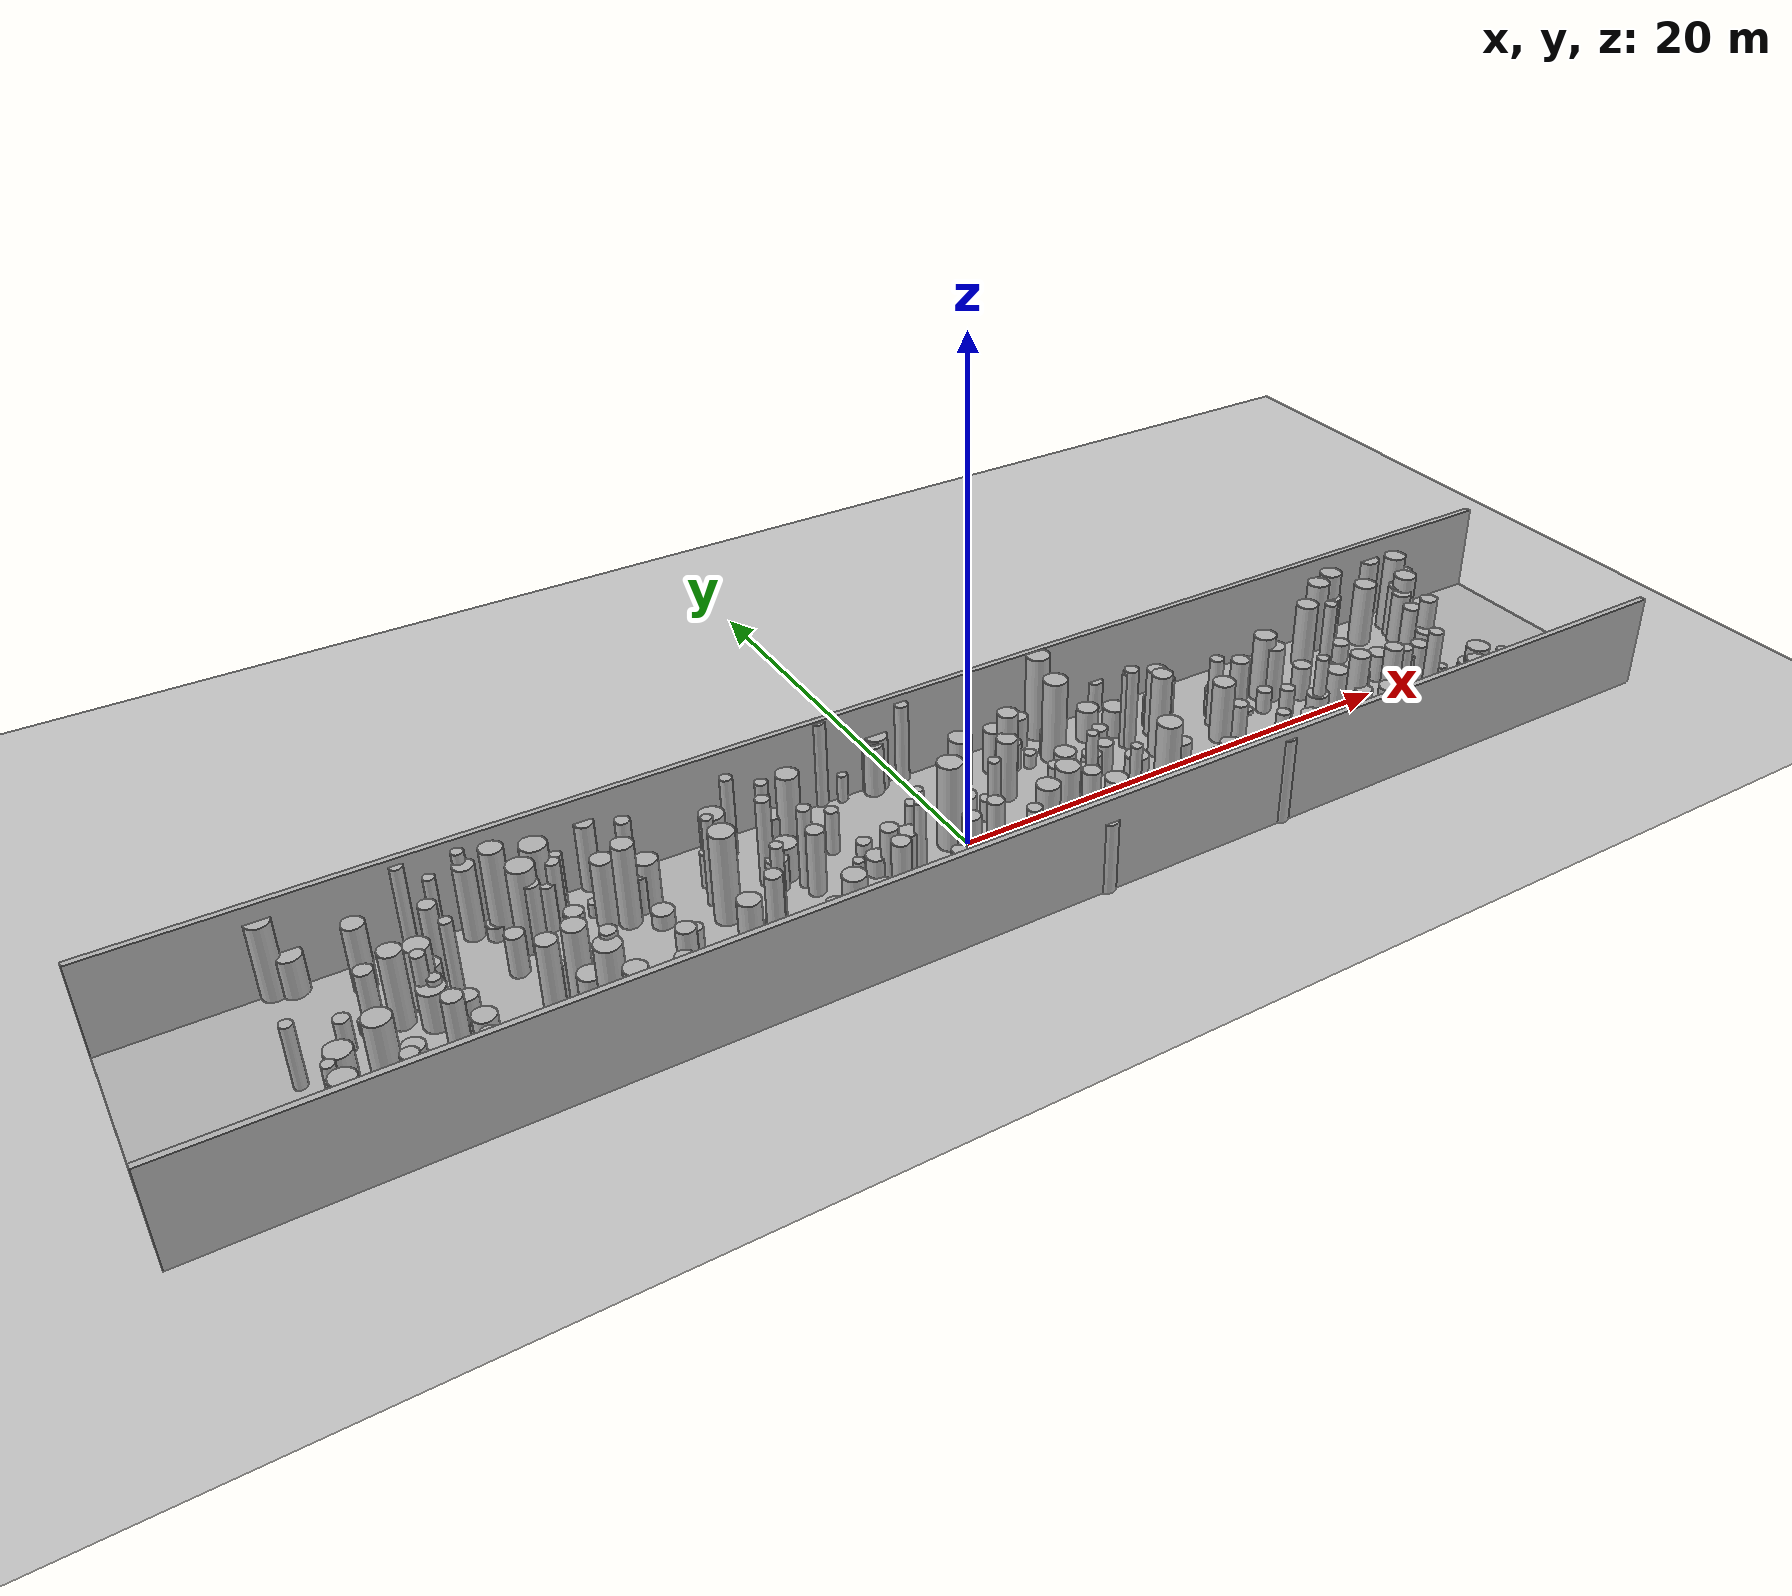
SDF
<?xml version="1.0"?>
<sdf version="1.4">
  <world name="default">
    <gui>
      <camera name="user_camera">
        <pose>-20 -30 40 0 0.66 0.83</pose>
      </camera>
    </gui>
    <include>
      <uri>model://ground_plane</uri>
    </include>
    <include>
      <uri>model://sun</uri>
    </include>
    <scene>
      <shadows>0</shadows>
    </scene>
    <model name="forest">
      <static>true</static>
      <link name="cylinder0">
        <pose>3.4628413697569584 -2.289347202412324 0.6654422106744277 0 0 0 </pose>
        <visual name="visual">
          <geometry>
            <cylinder>
              <radius>0.3623388396721826</radius>
              <length>1.3308844213488553</length>
            </cylinder>
          </geometry>
        </visual>
        <collision name="collision">
          <geometry>
            <cylinder>
              <radius>0.3623388396721826</radius>
              <length>1.3308844213488553</length>
            </cylinder>
          </geometry>
          <max_contacts>0</max_contacts>
        </collision>
      </link>
      <link name="cylinder1">
        <pose>6.147263556951511 -0.835973349621181 0.6341264469259545 0 0 0 </pose>
        <visual name="visual">
          <geometry>
            <cylinder>
              <radius>0.4507241850166356</radius>
              <length>1.268252893851909</length>
            </cylinder>
          </geometry>
        </visual>
        <collision name="collision">
          <geometry>
            <cylinder>
              <radius>0.4507241850166356</radius>
              <length>1.268252893851909</length>
            </cylinder>
          </geometry>
          <max_contacts>0</max_contacts>
        </collision>
      </link>
      <link name="cylinder2">
        <pose>3.094544353400803 2.1330752488763967 1.812567046464061 0 0 0 </pose>
        <visual name="visual">
          <geometry>
            <cylinder>
              <radius>0.4040577179959649</radius>
              <length>3.625134092928122</length>
            </cylinder>
          </geometry>
        </visual>
        <collision name="collision">
          <geometry>
            <cylinder>
              <radius>0.4040577179959649</radius>
              <length>3.625134092928122</length>
            </cylinder>
          </geometry>
          <max_contacts>0</max_contacts>
        </collision>
      </link>
      <link name="cylinder3">
        <pose>-13.713914897609564 -4.653162994623614 0.35892277264153055 0 0 0 </pose>
        <visual name="visual">
          <geometry>
            <cylinder>
              <radius>0.29627898533306785</radius>
              <length>0.7178455452830611</length>
            </cylinder>
          </geometry>
        </visual>
        <collision name="collision">
          <geometry>
            <cylinder>
              <radius>0.29627898533306785</radius>
              <length>0.7178455452830611</length>
            </cylinder>
          </geometry>
          <max_contacts>0</max_contacts>
        </collision>
      </link>
      <link name="cylinder4">
        <pose>-3.506984922951794 -0.21980165004955943 1.118413497285194 0 0 0 </pose>
        <visual name="visual">
          <geometry>
            <cylinder>
              <radius>0.33879364524942096</radius>
              <length>2.236826994570388</length>
            </cylinder>
          </geometry>
        </visual>
        <collision name="collision">
          <geometry>
            <cylinder>
              <radius>0.33879364524942096</radius>
              <length>2.236826994570388</length>
            </cylinder>
          </geometry>
          <max_contacts>0</max_contacts>
        </collision>
      </link>
      <link name="cylinder5">
        <pose>4.11257752636477 -0.46680314217459085 1.1587344306185745 0 0 0 </pose>
        <visual name="visual">
          <geometry>
            <cylinder>
              <radius>0.4856795118677984</radius>
              <length>2.317468861237149</length>
            </cylinder>
          </geometry>
        </visual>
        <collision name="collision">
          <geometry>
            <cylinder>
              <radius>0.4856795118677984</radius>
              <length>2.317468861237149</length>
            </cylinder>
          </geometry>
          <max_contacts>0</max_contacts>
        </collision>
      </link>
      <link name="cylinder6">
        <pose>-19.720187394413507 -0.7791817948835389 0.5384522503567314 0 0 0 </pose>
        <visual name="visual">
          <geometry>
            <cylinder>
              <radius>0.36325864529305907</radius>
              <length>1.0769045007134628</length>
            </cylinder>
          </geometry>
        </visual>
        <collision name="collision">
          <geometry>
            <cylinder>
              <radius>0.36325864529305907</radius>
              <length>1.0769045007134628</length>
            </cylinder>
          </geometry>
          <max_contacts>0</max_contacts>
        </collision>
      </link>
      <link name="cylinder7">
        <pose>21.736004291371536 -0.49966305445489834 0.8340649245499148 0 0 0 </pose>
        <visual name="visual">
          <geometry>
            <cylinder>
              <radius>0.20075408702600467</radius>
              <length>1.6681298490998295</length>
            </cylinder>
          </geometry>
        </visual>
        <collision name="collision">
          <geometry>
            <cylinder>
              <radius>0.20075408702600467</radius>
              <length>1.6681298490998295</length>
            </cylinder>
          </geometry>
          <max_contacts>0</max_contacts>
        </collision>
      </link>
      <link name="cylinder8">
        <pose>10.914736461077815 -3.8365037087492793 1.3696143019365636 0 0 0 </pose>
        <visual name="visual">
          <geometry>
            <cylinder>
              <radius>0.23327978234521513</radius>
              <length>2.7392286038731273</length>
            </cylinder>
          </geometry>
        </visual>
        <collision name="collision">
          <geometry>
            <cylinder>
              <radius>0.23327978234521513</radius>
              <length>2.7392286038731273</length>
            </cylinder>
          </geometry>
          <max_contacts>0</max_contacts>
        </collision>
      </link>
      <link name="cylinder9">
        <pose>14.853554070247391 -0.47774101991207996 1.1286734602600519 0 0 0 </pose>
        <visual name="visual">
          <geometry>
            <cylinder>
              <radius>0.2918521224820633</radius>
              <length>2.2573469205201038</length>
            </cylinder>
          </geometry>
        </visual>
        <collision name="collision">
          <geometry>
            <cylinder>
              <radius>0.2918521224820633</radius>
              <length>2.2573469205201038</length>
            </cylinder>
          </geometry>
          <max_contacts>0</max_contacts>
        </collision>
      </link>
      <link name="cylinder10">
        <pose>-22.94843817894639 0.8644904563835896 0.7978183880506935 0 0 0 </pose>
        <visual name="visual">
          <geometry>
            <cylinder>
              <radius>0.28195261213701345</radius>
              <length>1.595636776101387</length>
            </cylinder>
          </geometry>
        </visual>
        <collision name="collision">
          <geometry>
            <cylinder>
              <radius>0.28195261213701345</radius>
              <length>1.595636776101387</length>
            </cylinder>
          </geometry>
          <max_contacts>0</max_contacts>
        </collision>
      </link>
      <link name="cylinder11">
        <pose>-0.05825835961387327 4.739265958560516 1.8411400147356047 0 0 0 </pose>
        <visual name="visual">
          <geometry>
            <cylinder>
              <radius>0.2696441374136169</radius>
              <length>3.6822800294712095</length>
            </cylinder>
          </geometry>
        </visual>
        <collision name="collision">
          <geometry>
            <cylinder>
              <radius>0.2696441374136169</radius>
              <length>3.6822800294712095</length>
            </cylinder>
          </geometry>
          <max_contacts>0</max_contacts>
        </collision>
      </link>
      <link name="cylinder12">
        <pose>2.762917679618166 -4.942033731541792 1.4991604493968764 0 0 0 </pose>
        <visual name="visual">
          <geometry>
            <cylinder>
              <radius>0.3461101783480123</radius>
              <length>2.998320898793753</length>
            </cylinder>
          </geometry>
        </visual>
        <collision name="collision">
          <geometry>
            <cylinder>
              <radius>0.3461101783480123</radius>
              <length>2.998320898793753</length>
            </cylinder>
          </geometry>
          <max_contacts>0</max_contacts>
        </collision>
      </link>
      <link name="cylinder13">
        <pose>-8.825607430379932 3.061119883167377 1.0908622930355738 0 0 0 </pose>
        <visual name="visual">
          <geometry>
            <cylinder>
              <radius>0.25389053908064657</radius>
              <length>2.1817245860711476</length>
            </cylinder>
          </geometry>
        </visual>
        <collision name="collision">
          <geometry>
            <cylinder>
              <radius>0.25389053908064657</radius>
              <length>2.1817245860711476</length>
            </cylinder>
          </geometry>
          <max_contacts>0</max_contacts>
        </collision>
      </link>
      <link name="cylinder14">
        <pose>0.8877093643061151 -0.3338838715916195 1.8151710364971445 0 0 0 </pose>
        <visual name="visual">
          <geometry>
            <cylinder>
              <radius>0.23752691512128796</radius>
              <length>3.630342072994289</length>
            </cylinder>
          </geometry>
        </visual>
        <collision name="collision">
          <geometry>
            <cylinder>
              <radius>0.23752691512128796</radius>
              <length>3.630342072994289</length>
            </cylinder>
          </geometry>
          <max_contacts>0</max_contacts>
        </collision>
      </link>
      <link name="cylinder15">
        <pose>13.033938769299283 0.21987636582843706 0.8772535603588143 0 0 0 </pose>
        <visual name="visual">
          <geometry>
            <cylinder>
              <radius>0.32073914165574224</radius>
              <length>1.7545071207176286</length>
            </cylinder>
          </geometry>
        </visual>
        <collision name="collision">
          <geometry>
            <cylinder>
              <radius>0.32073914165574224</radius>
              <length>1.7545071207176286</length>
            </cylinder>
          </geometry>
          <max_contacts>0</max_contacts>
        </collision>
      </link>
      <link name="cylinder16">
        <pose>-14.915830762899091 1.4472085424360976 0.5644783765120763 0 0 0 </pose>
        <visual name="visual">
          <geometry>
            <cylinder>
              <radius>0.3948633694514866</radius>
              <length>1.1289567530241527</length>
            </cylinder>
          </geometry>
        </visual>
        <collision name="collision">
          <geometry>
            <cylinder>
              <radius>0.3948633694514866</radius>
              <length>1.1289567530241527</length>
            </cylinder>
          </geometry>
          <max_contacts>0</max_contacts>
        </collision>
      </link>
      <link name="cylinder17">
        <pose>2.6635914078259475 1.8422723856421488 1.0551088756825966 0 0 0 </pose>
        <visual name="visual">
          <geometry>
            <cylinder>
              <radius>0.28559733410241817</radius>
              <length>2.110217751365193</length>
            </cylinder>
          </geometry>
        </visual>
        <collision name="collision">
          <geometry>
            <cylinder>
              <radius>0.28559733410241817</radius>
              <length>2.110217751365193</length>
            </cylinder>
          </geometry>
          <max_contacts>0</max_contacts>
        </collision>
      </link>
      <link name="cylinder18">
        <pose>16.003366030238105 -1.0349550631368478 0.9583371634974845 0 0 0 </pose>
        <visual name="visual">
          <geometry>
            <cylinder>
              <radius>0.4483700065809316</radius>
              <length>1.916674326994969</length>
            </cylinder>
          </geometry>
        </visual>
        <collision name="collision">
          <geometry>
            <cylinder>
              <radius>0.4483700065809316</radius>
              <length>1.916674326994969</length>
            </cylinder>
          </geometry>
          <max_contacts>0</max_contacts>
        </collision>
      </link>
      <link name="cylinder19">
        <pose>-19.144880378357875 1.1213408445774533 1.868388934945783 0 0 0 </pose>
        <visual name="visual">
          <geometry>
            <cylinder>
              <radius>0.21957528042214602</radius>
              <length>3.736777869891566</length>
            </cylinder>
          </geometry>
        </visual>
        <collision name="collision">
          <geometry>
            <cylinder>
              <radius>0.21957528042214602</radius>
              <length>3.736777869891566</length>
            </cylinder>
          </geometry>
          <max_contacts>0</max_contacts>
        </collision>
      </link>
      <link name="cylinder20">
        <pose>-19.71496856231309 -4.511685920978579 1.7659162823239158 0 0 0 </pose>
        <visual name="visual">
          <geometry>
            <cylinder>
              <radius>0.33204822793152555</radius>
              <length>3.5318325646478317</length>
            </cylinder>
          </geometry>
        </visual>
        <collision name="collision">
          <geometry>
            <cylinder>
              <radius>0.33204822793152555</radius>
              <length>3.5318325646478317</length>
            </cylinder>
          </geometry>
          <max_contacts>0</max_contacts>
        </collision>
      </link>
      <link name="cylinder21">
        <pose>19.082661327178926 3.3031229890450327 1.54602594841249 0 0 0 </pose>
        <visual name="visual">
          <geometry>
            <cylinder>
              <radius>0.4556177747040008</radius>
              <length>3.09205189682498</length>
            </cylinder>
          </geometry>
        </visual>
        <collision name="collision">
          <geometry>
            <cylinder>
              <radius>0.4556177747040008</radius>
              <length>3.09205189682498</length>
            </cylinder>
          </geometry>
          <max_contacts>0</max_contacts>
        </collision>
      </link>
      <link name="cylinder22">
        <pose>24.895594062170886 3.5237761898894107 1.4979125226563086 0 0 0 </pose>
        <visual name="visual">
          <geometry>
            <cylinder>
              <radius>0.2958457283532197</radius>
              <length>2.995825045312617</length>
            </cylinder>
          </geometry>
        </visual>
        <collision name="collision">
          <geometry>
            <cylinder>
              <radius>0.2958457283532197</radius>
              <length>2.995825045312617</length>
            </cylinder>
          </geometry>
          <max_contacts>0</max_contacts>
        </collision>
      </link>
      <link name="cylinder23">
        <pose>3.1184100152640184 -3.3486202408034194 1.025314523484191 0 0 0 </pose>
        <visual name="visual">
          <geometry>
            <cylinder>
              <radius>0.43551143325337116</radius>
              <length>2.050629046968382</length>
            </cylinder>
          </geometry>
        </visual>
        <collision name="collision">
          <geometry>
            <cylinder>
              <radius>0.43551143325337116</radius>
              <length>2.050629046968382</length>
            </cylinder>
          </geometry>
          <max_contacts>0</max_contacts>
        </collision>
      </link>
      <link name="cylinder24">
        <pose>22.5454302663233 -3.163153579336604 1.5665030020215478 0 0 0 </pose>
        <visual name="visual">
          <geometry>
            <cylinder>
              <radius>0.46524977752787494</radius>
              <length>3.1330060040430956</length>
            </cylinder>
          </geometry>
        </visual>
        <collision name="collision">
          <geometry>
            <cylinder>
              <radius>0.46524977752787494</radius>
              <length>3.1330060040430956</length>
            </cylinder>
          </geometry>
          <max_contacts>0</max_contacts>
        </collision>
      </link>
      <link name="cylinder25">
        <pose>-5.387020528179072 -3.762625480102729 1.0475717393415385 0 0 0 </pose>
        <visual name="visual">
          <geometry>
            <cylinder>
              <radius>0.31639036446640323</radius>
              <length>2.095143478683077</length>
            </cylinder>
          </geometry>
        </visual>
        <collision name="collision">
          <geometry>
            <cylinder>
              <radius>0.31639036446640323</radius>
              <length>2.095143478683077</length>
            </cylinder>
          </geometry>
          <max_contacts>0</max_contacts>
        </collision>
      </link>
      <link name="cylinder26">
        <pose>20.730629949656297 1.050386423845846 0.5811819108139609 0 0 0 </pose>
        <visual name="visual">
          <geometry>
            <cylinder>
              <radius>0.21628738374586193</radius>
              <length>1.1623638216279217</length>
            </cylinder>
          </geometry>
        </visual>
        <collision name="collision">
          <geometry>
            <cylinder>
              <radius>0.21628738374586193</radius>
              <length>1.1623638216279217</length>
            </cylinder>
          </geometry>
          <max_contacts>0</max_contacts>
        </collision>
      </link>
      <link name="cylinder27">
        <pose>11.89219978713949 -2.0400406789135896 0.6957856865702874 0 0 0 </pose>
        <visual name="visual">
          <geometry>
            <cylinder>
              <radius>0.3196928371164899</radius>
              <length>1.3915713731405748</length>
            </cylinder>
          </geometry>
        </visual>
        <collision name="collision">
          <geometry>
            <cylinder>
              <radius>0.3196928371164899</radius>
              <length>1.3915713731405748</length>
            </cylinder>
          </geometry>
          <max_contacts>0</max_contacts>
        </collision>
      </link>
      <link name="cylinder28">
        <pose>-13.318579847116085 -4.334735547061642 1.752126669545675 0 0 0 </pose>
        <visual name="visual">
          <geometry>
            <cylinder>
              <radius>0.3174813889196501</radius>
              <length>3.50425333909135</length>
            </cylinder>
          </geometry>
        </visual>
        <collision name="collision">
          <geometry>
            <cylinder>
              <radius>0.3174813889196501</radius>
              <length>3.50425333909135</length>
            </cylinder>
          </geometry>
          <max_contacts>0</max_contacts>
        </collision>
      </link>
      <link name="cylinder29">
        <pose>6.236275831533405 0.9180804808281193 0.6771144392514992 0 0 0 </pose>
        <visual name="visual">
          <geometry>
            <cylinder>
              <radius>0.39991615061004826</radius>
              <length>1.3542288785029983</length>
            </cylinder>
          </geometry>
        </visual>
        <collision name="collision">
          <geometry>
            <cylinder>
              <radius>0.39991615061004826</radius>
              <length>1.3542288785029983</length>
            </cylinder>
          </geometry>
          <max_contacts>0</max_contacts>
        </collision>
      </link>
      <link name="cylinder30">
        <pose>-11.995854792915667 2.4163197238553105 0.9038290726874816 0 0 0 </pose>
        <visual name="visual">
          <geometry>
            <cylinder>
              <radius>0.21869572624127953</radius>
              <length>1.8076581453749632</length>
            </cylinder>
          </geometry>
        </visual>
        <collision name="collision">
          <geometry>
            <cylinder>
              <radius>0.21869572624127953</radius>
              <length>1.8076581453749632</length>
            </cylinder>
          </geometry>
          <max_contacts>0</max_contacts>
        </collision>
      </link>
      <link name="cylinder31">
        <pose>3.9573640115104993 3.118142987065667 0.7258819883004495 0 0 0 </pose>
        <visual name="visual">
          <geometry>
            <cylinder>
              <radius>0.38532866954467454</radius>
              <length>1.451763976600899</length>
            </cylinder>
          </geometry>
        </visual>
        <collision name="collision">
          <geometry>
            <cylinder>
              <radius>0.38532866954467454</radius>
              <length>1.451763976600899</length>
            </cylinder>
          </geometry>
          <max_contacts>0</max_contacts>
        </collision>
      </link>
      <link name="cylinder32">
        <pose>-0.5486599307565783 -4.5450918794384325 1.128984314593845 0 0 0 </pose>
        <visual name="visual">
          <geometry>
            <cylinder>
              <radius>0.3287161685269954</radius>
              <length>2.25796862918769</length>
            </cylinder>
          </geometry>
        </visual>
        <collision name="collision">
          <geometry>
            <cylinder>
              <radius>0.3287161685269954</radius>
              <length>2.25796862918769</length>
            </cylinder>
          </geometry>
          <max_contacts>0</max_contacts>
        </collision>
      </link>
      <link name="cylinder33">
        <pose>-18.896950440802375 -0.6931139422170549 0.49911211689411256 0 0 0 </pose>
        <visual name="visual">
          <geometry>
            <cylinder>
              <radius>0.4333925284390563</radius>
              <length>0.9982242337882251</length>
            </cylinder>
          </geometry>
        </visual>
        <collision name="collision">
          <geometry>
            <cylinder>
              <radius>0.4333925284390563</radius>
              <length>0.9982242337882251</length>
            </cylinder>
          </geometry>
          <max_contacts>0</max_contacts>
        </collision>
      </link>
      <link name="cylinder34">
        <pose>23.639740567221693 1.6571022610729358 1.1962088232181292 0 0 0 </pose>
        <visual name="visual">
          <geometry>
            <cylinder>
              <radius>0.3714651775510792</radius>
              <length>2.3924176464362583</length>
            </cylinder>
          </geometry>
        </visual>
        <collision name="collision">
          <geometry>
            <cylinder>
              <radius>0.3714651775510792</radius>
              <length>2.3924176464362583</length>
            </cylinder>
          </geometry>
          <max_contacts>0</max_contacts>
        </collision>
      </link>
      <link name="cylinder35">
        <pose>15.758543139333042 2.1095232941430435 1.585341498305851 0 0 0 </pose>
        <visual name="visual">
          <geometry>
            <cylinder>
              <radius>0.45787230308438437</radius>
              <length>3.170682996611702</length>
            </cylinder>
          </geometry>
        </visual>
        <collision name="collision">
          <geometry>
            <cylinder>
              <radius>0.45787230308438437</radius>
              <length>3.170682996611702</length>
            </cylinder>
          </geometry>
          <max_contacts>0</max_contacts>
        </collision>
      </link>
      <link name="cylinder36">
        <pose>-14.860128691754088 1.3980265653850674 1.0639077135778714 0 0 0 </pose>
        <visual name="visual">
          <geometry>
            <cylinder>
              <radius>0.3502826349452669</radius>
              <length>2.127815427155743</length>
            </cylinder>
          </geometry>
        </visual>
        <collision name="collision">
          <geometry>
            <cylinder>
              <radius>0.3502826349452669</radius>
              <length>2.127815427155743</length>
            </cylinder>
          </geometry>
          <max_contacts>0</max_contacts>
        </collision>
      </link>
      <link name="cylinder37">
        <pose>-19.28204595331838 2.6946950249595076 1.7064514801910602 0 0 0 </pose>
        <visual name="visual">
          <geometry>
            <cylinder>
              <radius>0.30673878537179744</radius>
              <length>3.4129029603821204</length>
            </cylinder>
          </geometry>
        </visual>
        <collision name="collision">
          <geometry>
            <cylinder>
              <radius>0.30673878537179744</radius>
              <length>3.4129029603821204</length>
            </cylinder>
          </geometry>
          <max_contacts>0</max_contacts>
        </collision>
      </link>
      <link name="cylinder38">
        <pose>-21.622168253205782 -3.528277166893835 0.8854798778643833 0 0 0 </pose>
        <visual name="visual">
          <geometry>
            <cylinder>
              <radius>0.3737616940321298</radius>
              <length>1.7709597557287666</length>
            </cylinder>
          </geometry>
        </visual>
        <collision name="collision">
          <geometry>
            <cylinder>
              <radius>0.3737616940321298</radius>
              <length>1.7709597557287666</length>
            </cylinder>
          </geometry>
          <max_contacts>0</max_contacts>
        </collision>
      </link>
      <link name="cylinder39">
        <pose>1.0107388010496372 -2.806590820150193 1.473025414406747 0 0 0 </pose>
        <visual name="visual">
          <geometry>
            <cylinder>
              <radius>0.2869115808181266</radius>
              <length>2.946050828813494</length>
            </cylinder>
          </geometry>
        </visual>
        <collision name="collision">
          <geometry>
            <cylinder>
              <radius>0.2869115808181266</radius>
              <length>2.946050828813494</length>
            </cylinder>
          </geometry>
          <max_contacts>0</max_contacts>
        </collision>
      </link>
      <link name="cylinder40">
        <pose>1.6088701362816984 -4.1246632977485245 1.0534164559563515 0 0 0 </pose>
        <visual name="visual">
          <geometry>
            <cylinder>
              <radius>0.48825325148155635</radius>
              <length>2.106832911912703</length>
            </cylinder>
          </geometry>
        </visual>
        <collision name="collision">
          <geometry>
            <cylinder>
              <radius>0.48825325148155635</radius>
              <length>2.106832911912703</length>
            </cylinder>
          </geometry>
          <max_contacts>0</max_contacts>
        </collision>
      </link>
      <link name="cylinder41">
        <pose>-12.65239928357816 2.0945600030771727 1.8282188372809236 0 0 0 </pose>
        <visual name="visual">
          <geometry>
            <cylinder>
              <radius>0.40592139253777537</radius>
              <length>3.656437674561847</length>
            </cylinder>
          </geometry>
        </visual>
        <collision name="collision">
          <geometry>
            <cylinder>
              <radius>0.40592139253777537</radius>
              <length>3.656437674561847</length>
            </cylinder>
          </geometry>
          <max_contacts>0</max_contacts>
        </collision>
      </link>
      <link name="cylinder42">
        <pose>-2.7956715817467845 -1.1946023405073234 1.8268806436719403 0 0 0 </pose>
        <visual name="visual">
          <geometry>
            <cylinder>
              <radius>0.2142210281344622</radius>
              <length>3.6537612873438805</length>
            </cylinder>
          </geometry>
        </visual>
        <collision name="collision">
          <geometry>
            <cylinder>
              <radius>0.2142210281344622</radius>
              <length>3.6537612873438805</length>
            </cylinder>
          </geometry>
          <max_contacts>0</max_contacts>
        </collision>
      </link>
      <link name="cylinder43">
        <pose>-1.3618833687806848 4.812034877058039 1.2369376812254034 0 0 0 </pose>
        <visual name="visual">
          <geometry>
            <cylinder>
              <radius>0.3997781385621699</radius>
              <length>2.4738753624508067</length>
            </cylinder>
          </geometry>
        </visual>
        <collision name="collision">
          <geometry>
            <cylinder>
              <radius>0.3997781385621699</radius>
              <length>2.4738753624508067</length>
            </cylinder>
          </geometry>
          <max_contacts>0</max_contacts>
        </collision>
      </link>
      <link name="cylinder44">
        <pose>23.51437637090868 0.6806047675914328 1.6363686987049586 0 0 0 </pose>
        <visual name="visual">
          <geometry>
            <cylinder>
              <radius>0.3613377163619469</radius>
              <length>3.272737397409917</length>
            </cylinder>
          </geometry>
        </visual>
        <collision name="collision">
          <geometry>
            <cylinder>
              <radius>0.3613377163619469</radius>
              <length>3.272737397409917</length>
            </cylinder>
          </geometry>
          <max_contacts>0</max_contacts>
        </collision>
      </link>
      <link name="cylinder45">
        <pose>2.699982590883643 1.5658500669668278 1.4553408265392491 0 0 0 </pose>
        <visual name="visual">
          <geometry>
            <cylinder>
              <radius>0.40754068568707985</radius>
              <length>2.9106816530784982</length>
            </cylinder>
          </geometry>
        </visual>
        <collision name="collision">
          <geometry>
            <cylinder>
              <radius>0.40754068568707985</radius>
              <length>2.9106816530784982</length>
            </cylinder>
          </geometry>
          <max_contacts>0</max_contacts>
        </collision>
      </link>
      <link name="cylinder46">
        <pose>4.675669980994108 2.871554189658556 0.4341254402987136 0 0 0 </pose>
        <visual name="visual">
          <geometry>
            <cylinder>
              <radius>0.24977853423507435</radius>
              <length>0.8682508805974272</length>
            </cylinder>
          </geometry>
        </visual>
        <collision name="collision">
          <geometry>
            <cylinder>
              <radius>0.24977853423507435</radius>
              <length>0.8682508805974272</length>
            </cylinder>
          </geometry>
          <max_contacts>0</max_contacts>
        </collision>
      </link>
      <link name="cylinder47">
        <pose>10.79666071523338 -1.2056584372661083 0.5084493877864421 0 0 0 </pose>
        <visual name="visual">
          <geometry>
            <cylinder>
              <radius>0.31588122362945537</radius>
              <length>1.0168987755728842</length>
            </cylinder>
          </geometry>
        </visual>
        <collision name="collision">
          <geometry>
            <cylinder>
              <radius>0.31588122362945537</radius>
              <length>1.0168987755728842</length>
            </cylinder>
          </geometry>
          <max_contacts>0</max_contacts>
        </collision>
      </link>
      <link name="cylinder48">
        <pose>-11.61964310736973 -4.4868902401587905 1.59967877188241 0 0 0 </pose>
        <visual name="visual">
          <geometry>
            <cylinder>
              <radius>0.2268719857978892</radius>
              <length>3.19935754376482</length>
            </cylinder>
          </geometry>
        </visual>
        <collision name="collision">
          <geometry>
            <cylinder>
              <radius>0.2268719857978892</radius>
              <length>3.19935754376482</length>
            </cylinder>
          </geometry>
          <max_contacts>0</max_contacts>
        </collision>
      </link>
      <link name="cylinder49">
        <pose>7.6879416544727945 -0.06949785690728572 0.668260202787761 0 0 0 </pose>
        <visual name="visual">
          <geometry>
            <cylinder>
              <radius>0.4723194740101033</radius>
              <length>1.336520405575522</length>
            </cylinder>
          </geometry>
        </visual>
        <collision name="collision">
          <geometry>
            <cylinder>
              <radius>0.4723194740101033</radius>
              <length>1.336520405575522</length>
            </cylinder>
          </geometry>
          <max_contacts>0</max_contacts>
        </collision>
      </link>
      <link name="cylinder50">
        <pose>-11.674075723469363 2.605777790942094 1.1533279174148903 0 0 0 </pose>
        <visual name="visual">
          <geometry>
            <cylinder>
              <radius>0.429506536923171</radius>
              <length>2.3066558348297805</length>
            </cylinder>
          </geometry>
        </visual>
        <collision name="collision">
          <geometry>
            <cylinder>
              <radius>0.429506536923171</radius>
              <length>2.3066558348297805</length>
            </cylinder>
          </geometry>
          <max_contacts>0</max_contacts>
        </collision>
      </link>
      <link name="cylinder51">
        <pose>-9.448274268920775 2.6031974305453343 0.8548668410377662 0 0 0 </pose>
        <visual name="visual">
          <geometry>
            <cylinder>
              <radius>0.2059955484997469</radius>
              <length>1.7097336820755324</length>
            </cylinder>
          </geometry>
        </visual>
        <collision name="collision">
          <geometry>
            <cylinder>
              <radius>0.2059955484997469</radius>
              <length>1.7097336820755324</length>
            </cylinder>
          </geometry>
          <max_contacts>0</max_contacts>
        </collision>
      </link>
      <link name="cylinder52">
        <pose>24.189380151882077 3.0545982899948125 1.319124420648759 0 0 0 </pose>
        <visual name="visual">
          <geometry>
            <cylinder>
              <radius>0.4708666080646746</radius>
              <length>2.638248841297518</length>
            </cylinder>
          </geometry>
        </visual>
        <collision name="collision">
          <geometry>
            <cylinder>
              <radius>0.4708666080646746</radius>
              <length>2.638248841297518</length>
            </cylinder>
          </geometry>
          <max_contacts>0</max_contacts>
        </collision>
      </link>
      <link name="cylinder53">
        <pose>-21.52801347100941 3.6398916483327692 1.4734466359067553 0 0 0 </pose>
        <visual name="visual">
          <geometry>
            <cylinder>
              <radius>0.39693504497746435</radius>
              <length>2.9468932718135106</length>
            </cylinder>
          </geometry>
        </visual>
        <collision name="collision">
          <geometry>
            <cylinder>
              <radius>0.39693504497746435</radius>
              <length>2.9468932718135106</length>
            </cylinder>
          </geometry>
          <max_contacts>0</max_contacts>
        </collision>
      </link>
      <link name="cylinder54">
        <pose>-20.258095380870884 -2.7951237280175145 1.9691184251869394 0 0 0 </pose>
        <visual name="visual">
          <geometry>
            <cylinder>
              <radius>0.35025742521704517</radius>
              <length>3.9382368503738787</length>
            </cylinder>
          </geometry>
        </visual>
        <collision name="collision">
          <geometry>
            <cylinder>
              <radius>0.35025742521704517</radius>
              <length>3.9382368503738787</length>
            </cylinder>
          </geometry>
          <max_contacts>0</max_contacts>
        </collision>
      </link>
      <link name="cylinder55">
        <pose>-20.248304255392 0.9410187094456459 1.488160364582664 0 0 0 </pose>
        <visual name="visual">
          <geometry>
            <cylinder>
              <radius>0.24636967487454742</radius>
              <length>2.976320729165328</length>
            </cylinder>
          </geometry>
        </visual>
        <collision name="collision">
          <geometry>
            <cylinder>
              <radius>0.24636967487454742</radius>
              <length>2.976320729165328</length>
            </cylinder>
          </geometry>
          <max_contacts>0</max_contacts>
        </collision>
      </link>
      <link name="cylinder56">
        <pose>5.786715316405367 2.8610847154104864 1.9269355409061464 0 0 0 </pose>
        <visual name="visual">
          <geometry>
            <cylinder>
              <radius>0.4875926582956024</radius>
              <length>3.8538710818122928</length>
            </cylinder>
          </geometry>
        </visual>
        <collision name="collision">
          <geometry>
            <cylinder>
              <radius>0.4875926582956024</radius>
              <length>3.8538710818122928</length>
            </cylinder>
          </geometry>
          <max_contacts>0</max_contacts>
        </collision>
      </link>
      <link name="cylinder57">
        <pose>6.853827936471674 -3.4298371440562625 0.24526550884120013 0 0 0 </pose>
        <visual name="visual">
          <geometry>
            <cylinder>
              <radius>0.2015334120040986</radius>
              <length>0.49053101768240026</length>
            </cylinder>
          </geometry>
        </visual>
        <collision name="collision">
          <geometry>
            <cylinder>
              <radius>0.2015334120040986</radius>
              <length>0.49053101768240026</length>
            </cylinder>
          </geometry>
          <max_contacts>0</max_contacts>
        </collision>
      </link>
      <link name="cylinder58">
        <pose>4.77996997224507 1.2287385943814702 0.5858104529320367 0 0 0 </pose>
        <visual name="visual">
          <geometry>
            <cylinder>
              <radius>0.3166115571271382</radius>
              <length>1.1716209058640734</length>
            </cylinder>
          </geometry>
        </visual>
        <collision name="collision">
          <geometry>
            <cylinder>
              <radius>0.3166115571271382</radius>
              <length>1.1716209058640734</length>
            </cylinder>
          </geometry>
          <max_contacts>0</max_contacts>
        </collision>
      </link>
      <link name="cylinder59">
        <pose>-12.711289072214715 -3.9343882838865065 0.7482421376359194 0 0 0 </pose>
        <visual name="visual">
          <geometry>
            <cylinder>
              <radius>0.37233720048792596</radius>
              <length>1.4964842752718388</length>
            </cylinder>
          </geometry>
        </visual>
        <collision name="collision">
          <geometry>
            <cylinder>
              <radius>0.37233720048792596</radius>
              <length>1.4964842752718388</length>
            </cylinder>
          </geometry>
          <max_contacts>0</max_contacts>
        </collision>
      </link>
      <link name="cylinder60">
        <pose>-16.311451390738718 -0.43196650335526954 0.714466852662723 0 0 0 </pose>
        <visual name="visual">
          <geometry>
            <cylinder>
              <radius>0.28649936500409673</radius>
              <length>1.428933705325446</length>
            </cylinder>
          </geometry>
        </visual>
        <collision name="collision">
          <geometry>
            <cylinder>
              <radius>0.28649936500409673</radius>
              <length>1.428933705325446</length>
            </cylinder>
          </geometry>
          <max_contacts>0</max_contacts>
        </collision>
      </link>
      <link name="cylinder61">
        <pose>-19.582668314628947 4.818460122576868 1.8649378753256285 0 0 0 </pose>
        <visual name="visual">
          <geometry>
            <cylinder>
              <radius>0.23693553470796497</radius>
              <length>3.729875750651257</length>
            </cylinder>
          </geometry>
        </visual>
        <collision name="collision">
          <geometry>
            <cylinder>
              <radius>0.23693553470796497</radius>
              <length>3.729875750651257</length>
            </cylinder>
          </geometry>
          <max_contacts>0</max_contacts>
        </collision>
      </link>
      <link name="cylinder62">
        <pose>22.81225635890371 -2.625337753581205 1.021754991340225 0 0 0 </pose>
        <visual name="visual">
          <geometry>
            <cylinder>
              <radius>0.47015913966621276</radius>
              <length>2.04350998268045</length>
            </cylinder>
          </geometry>
        </visual>
        <collision name="collision">
          <geometry>
            <cylinder>
              <radius>0.47015913966621276</radius>
              <length>2.04350998268045</length>
            </cylinder>
          </geometry>
          <max_contacts>0</max_contacts>
        </collision>
      </link>
      <link name="cylinder63">
        <pose>-16.54296434246082 -0.6843838606454264 1.530939241829271 0 0 0 </pose>
        <visual name="visual">
          <geometry>
            <cylinder>
              <radius>0.3817170006206134</radius>
              <length>3.061878483658542</length>
            </cylinder>
          </geometry>
        </visual>
        <collision name="collision">
          <geometry>
            <cylinder>
              <radius>0.3817170006206134</radius>
              <length>3.061878483658542</length>
            </cylinder>
          </geometry>
          <max_contacts>0</max_contacts>
        </collision>
      </link>
      <link name="cylinder64">
        <pose>-8.045178185820813 -0.3580063951271928 1.6513341150544132 0 0 0 </pose>
        <visual name="visual">
          <geometry>
            <cylinder>
              <radius>0.23491665644662857</radius>
              <length>3.3026682301088264</length>
            </cylinder>
          </geometry>
        </visual>
        <collision name="collision">
          <geometry>
            <cylinder>
              <radius>0.23491665644662857</radius>
              <length>3.3026682301088264</length>
            </cylinder>
          </geometry>
          <max_contacts>0</max_contacts>
        </collision>
      </link>
      <link name="cylinder65">
        <pose>9.52588501337528 0.9576877747168311 1.943984391102354 0 0 0 </pose>
        <visual name="visual">
          <geometry>
            <cylinder>
              <radius>0.40799603967908904</radius>
              <length>3.887968782204708</length>
            </cylinder>
          </geometry>
        </visual>
        <collision name="collision">
          <geometry>
            <cylinder>
              <radius>0.40799603967908904</radius>
              <length>3.887968782204708</length>
            </cylinder>
          </geometry>
          <max_contacts>0</max_contacts>
        </collision>
      </link>
      <link name="cylinder66">
        <pose>-4.755308234507233 -0.16865954887539303 0.6221579891203828 0 0 0 </pose>
        <visual name="visual">
          <geometry>
            <cylinder>
              <radius>0.2161028084125902</radius>
              <length>1.2443159782407656</length>
            </cylinder>
          </geometry>
        </visual>
        <collision name="collision">
          <geometry>
            <cylinder>
              <radius>0.2161028084125902</radius>
              <length>1.2443159782407656</length>
            </cylinder>
          </geometry>
          <max_contacts>0</max_contacts>
        </collision>
      </link>
      <link name="cylinder67">
        <pose>19.270884500488513 -0.1999504821009923 0.6958926026865883 0 0 0 </pose>
        <visual name="visual">
          <geometry>
            <cylinder>
              <radius>0.2805599144375513</radius>
              <length>1.3917852053731765</length>
            </cylinder>
          </geometry>
        </visual>
        <collision name="collision">
          <geometry>
            <cylinder>
              <radius>0.2805599144375513</radius>
              <length>1.3917852053731765</length>
            </cylinder>
          </geometry>
          <max_contacts>0</max_contacts>
        </collision>
      </link>
      <link name="cylinder68">
        <pose>21.318692989701752 -2.758823897062268 0.404940197494045 0 0 0 </pose>
        <visual name="visual">
          <geometry>
            <cylinder>
              <radius>0.29693361762981957</radius>
              <length>0.80988039498809</length>
            </cylinder>
          </geometry>
        </visual>
        <collision name="collision">
          <geometry>
            <cylinder>
              <radius>0.29693361762981957</radius>
              <length>0.80988039498809</length>
            </cylinder>
          </geometry>
          <max_contacts>0</max_contacts>
        </collision>
      </link>
      <link name="cylinder69">
        <pose>1.6545361049470735 3.2540781081461585 1.2047178783333687 0 0 0 </pose>
        <visual name="visual">
          <geometry>
            <cylinder>
              <radius>0.4669682752164923</radius>
              <length>2.4094357566667375</length>
            </cylinder>
          </geometry>
        </visual>
        <collision name="collision">
          <geometry>
            <cylinder>
              <radius>0.4669682752164923</radius>
              <length>2.4094357566667375</length>
            </cylinder>
          </geometry>
          <max_contacts>0</max_contacts>
        </collision>
      </link>
      <link name="cylinder70">
        <pose>23.981804374284458 4.8808893762459356 1.5759080402624706 0 0 0 </pose>
        <visual name="visual">
          <geometry>
            <cylinder>
              <radius>0.4524087115823557</radius>
              <length>3.151816080524941</length>
            </cylinder>
          </geometry>
        </visual>
        <collision name="collision">
          <geometry>
            <cylinder>
              <radius>0.4524087115823557</radius>
              <length>3.151816080524941</length>
            </cylinder>
          </geometry>
          <max_contacts>0</max_contacts>
        </collision>
      </link>
      <link name="cylinder71">
        <pose>-1.8663669013866055 0.9736581774018553 1.0069761986198955 0 0 0 </pose>
        <visual name="visual">
          <geometry>
            <cylinder>
              <radius>0.2519400063776923</radius>
              <length>2.013952397239791</length>
            </cylinder>
          </geometry>
        </visual>
        <collision name="collision">
          <geometry>
            <cylinder>
              <radius>0.2519400063776923</radius>
              <length>2.013952397239791</length>
            </cylinder>
          </geometry>
          <max_contacts>0</max_contacts>
        </collision>
      </link>
      <link name="cylinder72">
        <pose>-11.705516170306563 1.414088950837412 0.43539878525196707 0 0 0 </pose>
        <visual name="visual">
          <geometry>
            <cylinder>
              <radius>0.4109915763745654</radius>
              <length>0.8707975705039341</length>
            </cylinder>
          </geometry>
        </visual>
        <collision name="collision">
          <geometry>
            <cylinder>
              <radius>0.4109915763745654</radius>
              <length>0.8707975705039341</length>
            </cylinder>
          </geometry>
          <max_contacts>0</max_contacts>
        </collision>
      </link>
      <link name="cylinder73">
        <pose>-21.031636141422965 1.1885612521935665 1.6455285271103715 0 0 0 </pose>
        <visual name="visual">
          <geometry>
            <cylinder>
              <radius>0.4101022583487687</radius>
              <length>3.291057054220743</length>
            </cylinder>
          </geometry>
        </visual>
        <collision name="collision">
          <geometry>
            <cylinder>
              <radius>0.4101022583487687</radius>
              <length>3.291057054220743</length>
            </cylinder>
          </geometry>
          <max_contacts>0</max_contacts>
        </collision>
      </link>
      <link name="cylinder74">
        <pose>3.2904460794392065 3.4093247863137783 1.0771336419706645 0 0 0 </pose>
        <visual name="visual">
          <geometry>
            <cylinder>
              <radius>0.4006232998613821</radius>
              <length>2.154267283941329</length>
            </cylinder>
          </geometry>
        </visual>
        <collision name="collision">
          <geometry>
            <cylinder>
              <radius>0.4006232998613821</radius>
              <length>2.154267283941329</length>
            </cylinder>
          </geometry>
          <max_contacts>0</max_contacts>
        </collision>
      </link>
      <link name="cylinder75">
        <pose>12.285998100978205 0.44289316514971144 1.4467364115683354 0 0 0 </pose>
        <visual name="visual">
          <geometry>
            <cylinder>
              <radius>0.4491158269163352</radius>
              <length>2.893472823136671</length>
            </cylinder>
          </geometry>
        </visual>
        <collision name="collision">
          <geometry>
            <cylinder>
              <radius>0.4491158269163352</radius>
              <length>2.893472823136671</length>
            </cylinder>
          </geometry>
          <max_contacts>0</max_contacts>
        </collision>
      </link>
      <link name="cylinder76">
        <pose>-10.731984836244191 -2.3555092584488024 0.6043939121690365 0 0 0 </pose>
        <visual name="visual">
          <geometry>
            <cylinder>
              <radius>0.320633611367265</radius>
              <length>1.208787824338073</length>
            </cylinder>
          </geometry>
        </visual>
        <collision name="collision">
          <geometry>
            <cylinder>
              <radius>0.320633611367265</radius>
              <length>1.208787824338073</length>
            </cylinder>
          </geometry>
          <max_contacts>0</max_contacts>
        </collision>
      </link>
      <link name="cylinder77">
        <pose>5.629155065892995 0.2879845286221627 0.6309809773300655 0 0 0 </pose>
        <visual name="visual">
          <geometry>
            <cylinder>
              <radius>0.43257338801105366</radius>
              <length>1.261961954660131</length>
            </cylinder>
          </geometry>
        </visual>
        <collision name="collision">
          <geometry>
            <cylinder>
              <radius>0.43257338801105366</radius>
              <length>1.261961954660131</length>
            </cylinder>
          </geometry>
          <max_contacts>0</max_contacts>
        </collision>
      </link>
      <link name="cylinder78">
        <pose>0.8715351758022685 -2.4282599244527803 0.6046063216203329 0 0 0 </pose>
        <visual name="visual">
          <geometry>
            <cylinder>
              <radius>0.4758751512504867</radius>
              <length>1.2092126432406658</length>
            </cylinder>
          </geometry>
        </visual>
        <collision name="collision">
          <geometry>
            <cylinder>
              <radius>0.4758751512504867</radius>
              <length>1.2092126432406658</length>
            </cylinder>
          </geometry>
          <max_contacts>0</max_contacts>
        </collision>
      </link>
      <link name="cylinder79">
        <pose>23.875869095028435 2.5764015123100936 1.2880640875802067 0 0 0 </pose>
        <visual name="visual">
          <geometry>
            <cylinder>
              <radius>0.40085486248108526</radius>
              <length>2.5761281751604135</length>
            </cylinder>
          </geometry>
        </visual>
        <collision name="collision">
          <geometry>
            <cylinder>
              <radius>0.40085486248108526</radius>
              <length>2.5761281751604135</length>
            </cylinder>
          </geometry>
          <max_contacts>0</max_contacts>
        </collision>
      </link>
      <link name="cylinder80">
        <pose>-23.547237608411248 4.661717898071235 0.9072992125374453 0 0 0 </pose>
        <visual name="visual">
          <geometry>
            <cylinder>
              <radius>0.4698943906556807</radius>
              <length>1.8145984250748906</length>
            </cylinder>
          </geometry>
        </visual>
        <collision name="collision">
          <geometry>
            <cylinder>
              <radius>0.4698943906556807</radius>
              <length>1.8145984250748906</length>
            </cylinder>
          </geometry>
          <max_contacts>0</max_contacts>
        </collision>
      </link>
      <link name="cylinder81">
        <pose>13.494713009334156 -4.465588300839338 1.4067591082952307 0 0 0 </pose>
        <visual name="visual">
          <geometry>
            <cylinder>
              <radius>0.3812167118206994</radius>
              <length>2.8135182165904613</length>
            </cylinder>
          </geometry>
        </visual>
        <collision name="collision">
          <geometry>
            <cylinder>
              <radius>0.3812167118206994</radius>
              <length>2.8135182165904613</length>
            </cylinder>
          </geometry>
          <max_contacts>0</max_contacts>
        </collision>
      </link>
      <link name="cylinder82">
        <pose>-8.699680272153731 -1.0871776547090803 0.4847785946909561 0 0 0 </pose>
        <visual name="visual">
          <geometry>
            <cylinder>
              <radius>0.2513691433899134</radius>
              <length>0.9695571893819122</length>
            </cylinder>
          </geometry>
        </visual>
        <collision name="collision">
          <geometry>
            <cylinder>
              <radius>0.2513691433899134</radius>
              <length>0.9695571893819122</length>
            </cylinder>
          </geometry>
          <max_contacts>0</max_contacts>
        </collision>
      </link>
      <link name="cylinder83">
        <pose>15.139345639333854 1.1594362104256062 0.6174595633525808 0 0 0 </pose>
        <visual name="visual">
          <geometry>
            <cylinder>
              <radius>0.3080543960184824</radius>
              <length>1.2349191267051616</length>
            </cylinder>
          </geometry>
        </visual>
        <collision name="collision">
          <geometry>
            <cylinder>
              <radius>0.3080543960184824</radius>
              <length>1.2349191267051616</length>
            </cylinder>
          </geometry>
          <max_contacts>0</max_contacts>
        </collision>
      </link>
      <link name="cylinder84">
        <pose>9.315859578121696 -3.5736198615112458 1.6262315979028008 0 0 0 </pose>
        <visual name="visual">
          <geometry>
            <cylinder>
              <radius>0.40707819342825735</radius>
              <length>3.2524631958056016</length>
            </cylinder>
          </geometry>
        </visual>
        <collision name="collision">
          <geometry>
            <cylinder>
              <radius>0.40707819342825735</radius>
              <length>3.2524631958056016</length>
            </cylinder>
          </geometry>
          <max_contacts>0</max_contacts>
        </collision>
      </link>
      <link name="cylinder85">
        <pose>0.7863910488625763 1.548576271408857 0.5280076051594295 0 0 0 </pose>
        <visual name="visual">
          <geometry>
            <cylinder>
              <radius>0.4722202793988006</radius>
              <length>1.056015210318859</length>
            </cylinder>
          </geometry>
        </visual>
        <collision name="collision">
          <geometry>
            <cylinder>
              <radius>0.4722202793988006</radius>
              <length>1.056015210318859</length>
            </cylinder>
          </geometry>
          <max_contacts>0</max_contacts>
        </collision>
      </link>
      <link name="cylinder86">
        <pose>-5.568193708116237 1.5223996841351264 0.4909826445302055 0 0 0 </pose>
        <visual name="visual">
          <geometry>
            <cylinder>
              <radius>0.24527921551812176</radius>
              <length>0.981965289060411</length>
            </cylinder>
          </geometry>
        </visual>
        <collision name="collision">
          <geometry>
            <cylinder>
              <radius>0.24527921551812176</radius>
              <length>0.981965289060411</length>
            </cylinder>
          </geometry>
          <max_contacts>0</max_contacts>
        </collision>
      </link>
      <link name="cylinder87">
        <pose>-4.439568451101994 -2.685980406363566 1.7570160765028378 0 0 0 </pose>
        <visual name="visual">
          <geometry>
            <cylinder>
              <radius>0.3541496494956593</radius>
              <length>3.5140321530056755</length>
            </cylinder>
          </geometry>
        </visual>
        <collision name="collision">
          <geometry>
            <cylinder>
              <radius>0.3541496494956593</radius>
              <length>3.5140321530056755</length>
            </cylinder>
          </geometry>
          <max_contacts>0</max_contacts>
        </collision>
      </link>
      <link name="cylinder88">
        <pose>17.116260911705616 -3.801376694132834 1.6529892802913362 0 0 0 </pose>
        <visual name="visual">
          <geometry>
            <cylinder>
              <radius>0.4542084483008347</radius>
              <length>3.3059785605826724</length>
            </cylinder>
          </geometry>
        </visual>
        <collision name="collision">
          <geometry>
            <cylinder>
              <radius>0.4542084483008347</radius>
              <length>3.3059785605826724</length>
            </cylinder>
          </geometry>
          <max_contacts>0</max_contacts>
        </collision>
      </link>
      <link name="cylinder89">
        <pose>-9.664251049753126 0.5089138179898356 1.9934408992164934 0 0 0 </pose>
        <visual name="visual">
          <geometry>
            <cylinder>
              <radius>0.47892854912935545</radius>
              <length>3.9868817984329867</length>
            </cylinder>
          </geometry>
        </visual>
        <collision name="collision">
          <geometry>
            <cylinder>
              <radius>0.47892854912935545</radius>
              <length>3.9868817984329867</length>
            </cylinder>
          </geometry>
          <max_contacts>0</max_contacts>
        </collision>
      </link>
      <link name="cylinder90">
        <pose>-22.307128640391845 -1.498227058876397 1.547562607182266 0 0 0 </pose>
        <visual name="visual">
          <geometry>
            <cylinder>
              <radius>0.4866022356289181</radius>
              <length>3.095125214364532</length>
            </cylinder>
          </geometry>
        </visual>
        <collision name="collision">
          <geometry>
            <cylinder>
              <radius>0.4866022356289181</radius>
              <length>3.095125214364532</length>
            </cylinder>
          </geometry>
          <max_contacts>0</max_contacts>
        </collision>
      </link>
      <link name="cylinder91">
        <pose>10.64326766857262 2.730819315357367 0.7386741887547783 0 0 0 </pose>
        <visual name="visual">
          <geometry>
            <cylinder>
              <radius>0.4574239300209553</radius>
              <length>1.4773483775095566</length>
            </cylinder>
          </geometry>
        </visual>
        <collision name="collision">
          <geometry>
            <cylinder>
              <radius>0.4574239300209553</radius>
              <length>1.4773483775095566</length>
            </cylinder>
          </geometry>
          <max_contacts>0</max_contacts>
        </collision>
      </link>
      <link name="cylinder92">
        <pose>24.754883800228946 4.014134985091335 1.5978121512644732 0 0 0 </pose>
        <visual name="visual">
          <geometry>
            <cylinder>
              <radius>0.3995190786073297</radius>
              <length>3.1956243025289464</length>
            </cylinder>
          </geometry>
        </visual>
        <collision name="collision">
          <geometry>
            <cylinder>
              <radius>0.3995190786073297</radius>
              <length>3.1956243025289464</length>
            </cylinder>
          </geometry>
          <max_contacts>0</max_contacts>
        </collision>
      </link>
      <link name="cylinder93">
        <pose>9.787784097102808 1.0143147727902537 1.2169650770407832 0 0 0 </pose>
        <visual name="visual">
          <geometry>
            <cylinder>
              <radius>0.2940348147919326</radius>
              <length>2.4339301540815663</length>
            </cylinder>
          </geometry>
        </visual>
        <collision name="collision">
          <geometry>
            <cylinder>
              <radius>0.2940348147919326</radius>
              <length>2.4339301540815663</length>
            </cylinder>
          </geometry>
          <max_contacts>0</max_contacts>
        </collision>
      </link>
      <link name="cylinder94">
        <pose>-19.93070459955057 0.6989024922443621 1.0199618389779534 0 0 0 </pose>
        <visual name="visual">
          <geometry>
            <cylinder>
              <radius>0.24335262019357187</radius>
              <length>2.039923677955907</length>
            </cylinder>
          </geometry>
        </visual>
        <collision name="collision">
          <geometry>
            <cylinder>
              <radius>0.24335262019357187</radius>
              <length>2.039923677955907</length>
            </cylinder>
          </geometry>
          <max_contacts>0</max_contacts>
        </collision>
      </link>
      <link name="cylinder95">
        <pose>-15.537048727417153 -0.5628699038007863 1.5763746500477476 0 0 0 </pose>
        <visual name="visual">
          <geometry>
            <cylinder>
              <radius>0.425338742533531</radius>
              <length>3.152749300095495</length>
            </cylinder>
          </geometry>
        </visual>
        <collision name="collision">
          <geometry>
            <cylinder>
              <radius>0.425338742533531</radius>
              <length>3.152749300095495</length>
            </cylinder>
          </geometry>
          <max_contacts>0</max_contacts>
        </collision>
      </link>
      <link name="cylinder96">
        <pose>17.13950595983009 1.2155253800292005 0.880882763529969 0 0 0 </pose>
        <visual name="visual">
          <geometry>
            <cylinder>
              <radius>0.3840960285534355</radius>
              <length>1.761765527059938</length>
            </cylinder>
          </geometry>
        </visual>
        <collision name="collision">
          <geometry>
            <cylinder>
              <radius>0.3840960285534355</radius>
              <length>1.761765527059938</length>
            </cylinder>
          </geometry>
          <max_contacts>0</max_contacts>
        </collision>
      </link>
      <link name="cylinder97">
        <pose>-6.280055123024216 0.17378152963462945 1.4786445508308952 0 0 0 </pose>
        <visual name="visual">
          <geometry>
            <cylinder>
              <radius>0.33567492497228507</radius>
              <length>2.9572891016617904</length>
            </cylinder>
          </geometry>
        </visual>
        <collision name="collision">
          <geometry>
            <cylinder>
              <radius>0.33567492497228507</radius>
              <length>2.9572891016617904</length>
            </cylinder>
          </geometry>
          <max_contacts>0</max_contacts>
        </collision>
      </link>
      <link name="cylinder98">
        <pose>-5.683671884689108 -4.412773708067476 1.2108211489341947 0 0 0 </pose>
        <visual name="visual">
          <geometry>
            <cylinder>
              <radius>0.42125182569411046</radius>
              <length>2.4216422978683894</length>
            </cylinder>
          </geometry>
        </visual>
        <collision name="collision">
          <geometry>
            <cylinder>
              <radius>0.42125182569411046</radius>
              <length>2.4216422978683894</length>
            </cylinder>
          </geometry>
          <max_contacts>0</max_contacts>
        </collision>
      </link>
      <link name="cylinder99">
        <pose>22.088131380178453 -1.279707438589016 1.5221204193777027 0 0 0 </pose>
        <visual name="visual">
          <geometry>
            <cylinder>
              <radius>0.30013229719420975</radius>
              <length>3.0442408387554054</length>
            </cylinder>
          </geometry>
        </visual>
        <collision name="collision">
          <geometry>
            <cylinder>
              <radius>0.30013229719420975</radius>
              <length>3.0442408387554054</length>
            </cylinder>
          </geometry>
          <max_contacts>0</max_contacts>
        </collision>
      </link>
      <link name="cylinder100">
        <pose>0.3949588504941097 -1.204371911087625 1.2726974808545013 0 0 0 </pose>
        <visual name="visual">
          <geometry>
            <cylinder>
              <radius>0.32508580447038293</radius>
              <length>2.5453949617090026</length>
            </cylinder>
          </geometry>
        </visual>
        <collision name="collision">
          <geometry>
            <cylinder>
              <radius>0.32508580447038293</radius>
              <length>2.5453949617090026</length>
            </cylinder>
          </geometry>
          <max_contacts>0</max_contacts>
        </collision>
      </link>
      <link name="cylinder101">
        <pose>-15.204031428692966 3.768416047026829 1.7995495246444722 0 0 0 </pose>
        <visual name="visual">
          <geometry>
            <cylinder>
              <radius>0.497481941004323</radius>
              <length>3.5990990492889443</length>
            </cylinder>
          </geometry>
        </visual>
        <collision name="collision">
          <geometry>
            <cylinder>
              <radius>0.497481941004323</radius>
              <length>3.5990990492889443</length>
            </cylinder>
          </geometry>
          <max_contacts>0</max_contacts>
        </collision>
      </link>
      <link name="cylinder102">
        <pose>7.6762216497336055 2.393394171760354 0.6262116841152856 0 0 0 </pose>
        <visual name="visual">
          <geometry>
            <cylinder>
              <radius>0.31420929099533573</radius>
              <length>1.2524233682305712</length>
            </cylinder>
          </geometry>
        </visual>
        <collision name="collision">
          <geometry>
            <cylinder>
              <radius>0.31420929099533573</radius>
              <length>1.2524233682305712</length>
            </cylinder>
          </geometry>
          <max_contacts>0</max_contacts>
        </collision>
      </link>
      <link name="cylinder103">
        <pose>20.267248818742154 -4.412821589530021 0.8790280508820247 0 0 0 </pose>
        <visual name="visual">
          <geometry>
            <cylinder>
              <radius>0.38550360461328015</radius>
              <length>1.7580561017640495</length>
            </cylinder>
          </geometry>
        </visual>
        <collision name="collision">
          <geometry>
            <cylinder>
              <radius>0.38550360461328015</radius>
              <length>1.7580561017640495</length>
            </cylinder>
          </geometry>
          <max_contacts>0</max_contacts>
        </collision>
      </link>
      <link name="cylinder104">
        <pose>5.423183167117568 1.559778758041702 0.6869246939322828 0 0 0 </pose>
        <visual name="visual">
          <geometry>
            <cylinder>
              <radius>0.4390323352045561</radius>
              <length>1.3738493878645657</length>
            </cylinder>
          </geometry>
        </visual>
        <collision name="collision">
          <geometry>
            <cylinder>
              <radius>0.4390323352045561</radius>
              <length>1.3738493878645657</length>
            </cylinder>
          </geometry>
          <max_contacts>0</max_contacts>
        </collision>
      </link>
      <link name="cylinder105">
        <pose>14.47920625635188 1.3143063965557866 0.21674340851733284 0 0 0 </pose>
        <visual name="visual">
          <geometry>
            <cylinder>
              <radius>0.21581332017324223</radius>
              <length>0.4334868170346657</length>
            </cylinder>
          </geometry>
        </visual>
        <collision name="collision">
          <geometry>
            <cylinder>
              <radius>0.21581332017324223</radius>
              <length>0.4334868170346657</length>
            </cylinder>
          </geometry>
          <max_contacts>0</max_contacts>
        </collision>
      </link>
      <link name="cylinder106">
        <pose>22.424943120783148 3.3683418935318734 1.5379945779519284 0 0 0 </pose>
        <visual name="visual">
          <geometry>
            <cylinder>
              <radius>0.471680818994294</radius>
              <length>3.075989155903857</length>
            </cylinder>
          </geometry>
        </visual>
        <collision name="collision">
          <geometry>
            <cylinder>
              <radius>0.471680818994294</radius>
              <length>3.075989155903857</length>
            </cylinder>
          </geometry>
          <max_contacts>0</max_contacts>
        </collision>
      </link>
      <link name="cylinder107">
        <pose>20.94113688988935 0.6535641328251014 0.730349436871468 0 0 0 </pose>
        <visual name="visual">
          <geometry>
            <cylinder>
              <radius>0.43752563233725494</radius>
              <length>1.460698873742936</length>
            </cylinder>
          </geometry>
        </visual>
        <collision name="collision">
          <geometry>
            <cylinder>
              <radius>0.43752563233725494</radius>
              <length>1.460698873742936</length>
            </cylinder>
          </geometry>
          <max_contacts>0</max_contacts>
        </collision>
      </link>
      <link name="cylinder108">
        <pose>13.893962614632372 -1.1146602577756424 0.34782154365869655 0 0 0 </pose>
        <visual name="visual">
          <geometry>
            <cylinder>
              <radius>0.26931264912325314</radius>
              <length>0.6956430873173931</length>
            </cylinder>
          </geometry>
        </visual>
        <collision name="collision">
          <geometry>
            <cylinder>
              <radius>0.26931264912325314</radius>
              <length>0.6956430873173931</length>
            </cylinder>
          </geometry>
          <max_contacts>0</max_contacts>
        </collision>
      </link>
      <link name="cylinder109">
        <pose>-16.217596100967967 -0.44247608949450523 0.8615755332349713 0 0 0 </pose>
        <visual name="visual">
          <geometry>
            <cylinder>
              <radius>0.26234511421405327</radius>
              <length>1.7231510664699425</length>
            </cylinder>
          </geometry>
        </visual>
        <collision name="collision">
          <geometry>
            <cylinder>
              <radius>0.26234511421405327</radius>
              <length>1.7231510664699425</length>
            </cylinder>
          </geometry>
          <max_contacts>0</max_contacts>
        </collision>
      </link>
      <link name="cylinder110">
        <pose>7.7510819586495785 3.3597650773901737 0.8345917979552995 0 0 0 </pose>
        <visual name="visual">
          <geometry>
            <cylinder>
              <radius>0.4416243301038907</radius>
              <length>1.669183595910599</length>
            </cylinder>
          </geometry>
        </visual>
        <collision name="collision">
          <geometry>
            <cylinder>
              <radius>0.4416243301038907</radius>
              <length>1.669183595910599</length>
            </cylinder>
          </geometry>
          <max_contacts>0</max_contacts>
        </collision>
      </link>
      <link name="cylinder111">
        <pose>19.825323557563294 2.651874386181788 1.593591050303939 0 0 0 </pose>
        <visual name="visual">
          <geometry>
            <cylinder>
              <radius>0.2644968624051822</radius>
              <length>3.187182100607878</length>
            </cylinder>
          </geometry>
        </visual>
        <collision name="collision">
          <geometry>
            <cylinder>
              <radius>0.2644968624051822</radius>
              <length>3.187182100607878</length>
            </cylinder>
          </geometry>
          <max_contacts>0</max_contacts>
        </collision>
      </link>
      <link name="cylinder112">
        <pose>-23.43448711848476 -3.7036496082767867 1.230458189649069 0 0 0 </pose>
        <visual name="visual">
          <geometry>
            <cylinder>
              <radius>0.3479156946797025</radius>
              <length>2.460916379298138</length>
            </cylinder>
          </geometry>
        </visual>
        <collision name="collision">
          <geometry>
            <cylinder>
              <radius>0.3479156946797025</radius>
              <length>2.460916379298138</length>
            </cylinder>
          </geometry>
          <max_contacts>0</max_contacts>
        </collision>
      </link>
      <link name="cylinder113">
        <pose>22.68134547461731 -1.2803934552953211 0.6073762550327231 0 0 0 </pose>
        <visual name="visual">
          <geometry>
            <cylinder>
              <radius>0.24688693951041635</radius>
              <length>1.2147525100654462</length>
            </cylinder>
          </geometry>
        </visual>
        <collision name="collision">
          <geometry>
            <cylinder>
              <radius>0.24688693951041635</radius>
              <length>1.2147525100654462</length>
            </cylinder>
          </geometry>
          <max_contacts>0</max_contacts>
        </collision>
      </link>
      <link name="cylinder114">
        <pose>-2.7224206583395656 4.732515727977894 0.7097052029546217 0 0 0 </pose>
        <visual name="visual">
          <geometry>
            <cylinder>
              <radius>0.20595763137236203</radius>
              <length>1.4194104059092434</length>
            </cylinder>
          </geometry>
        </visual>
        <collision name="collision">
          <geometry>
            <cylinder>
              <radius>0.20595763137236203</radius>
              <length>1.4194104059092434</length>
            </cylinder>
          </geometry>
          <max_contacts>0</max_contacts>
        </collision>
      </link>
      <link name="cylinder115">
        <pose>-13.297319464965762 2.5191761511442046 1.503509850485518 0 0 0 </pose>
        <visual name="visual">
          <geometry>
            <cylinder>
              <radius>0.40467422501779327</radius>
              <length>3.007019700971036</length>
            </cylinder>
          </geometry>
        </visual>
        <collision name="collision">
          <geometry>
            <cylinder>
              <radius>0.40467422501779327</radius>
              <length>3.007019700971036</length>
            </cylinder>
          </geometry>
          <max_contacts>0</max_contacts>
        </collision>
      </link>
      <link name="cylinder116">
        <pose>-13.544723851435265 3.1862904845567446 0.4117936563209377 0 0 0 </pose>
        <visual name="visual">
          <geometry>
            <cylinder>
              <radius>0.20365809842283808</radius>
              <length>0.8235873126418753</length>
            </cylinder>
          </geometry>
        </visual>
        <collision name="collision">
          <geometry>
            <cylinder>
              <radius>0.20365809842283808</radius>
              <length>0.8235873126418753</length>
            </cylinder>
          </geometry>
          <max_contacts>0</max_contacts>
        </collision>
      </link>
      <link name="cylinder117">
        <pose>-14.759970854919585 -3.748810886451449 1.6313199008229375 0 0 0 </pose>
        <visual name="visual">
          <geometry>
            <cylinder>
              <radius>0.41455009812777377</radius>
              <length>3.262639801645875</length>
            </cylinder>
          </geometry>
        </visual>
        <collision name="collision">
          <geometry>
            <cylinder>
              <radius>0.41455009812777377</radius>
              <length>3.262639801645875</length>
            </cylinder>
          </geometry>
          <max_contacts>0</max_contacts>
        </collision>
      </link>
      <link name="cylinder118">
        <pose>18.515974843568493 0.5208096356534666 0.6469413533172448 0 0 0 </pose>
        <visual name="visual">
          <geometry>
            <cylinder>
              <radius>0.2362523610086094</radius>
              <length>1.2938827066344896</length>
            </cylinder>
          </geometry>
        </visual>
        <collision name="collision">
          <geometry>
            <cylinder>
              <radius>0.2362523610086094</radius>
              <length>1.2938827066344896</length>
            </cylinder>
          </geometry>
          <max_contacts>0</max_contacts>
        </collision>
      </link>
      <link name="cylinder119">
        <pose>-2.66378308059252 -3.6314053258045487 1.516345776900242 0 0 0 </pose>
        <visual name="visual">
          <geometry>
            <cylinder>
              <radius>0.2964627098753851</radius>
              <length>3.032691553800484</length>
            </cylinder>
          </geometry>
        </visual>
        <collision name="collision">
          <geometry>
            <cylinder>
              <radius>0.2964627098753851</radius>
              <length>3.032691553800484</length>
            </cylinder>
          </geometry>
          <max_contacts>0</max_contacts>
        </collision>
      </link>
      <link name="cylinder120">
        <pose>-22.167185689000945 1.433938770246403 0.3713698388362926 0 0 0 </pose>
        <visual name="visual">
          <geometry>
            <cylinder>
              <radius>0.23065739467556007</radius>
              <length>0.7427396776725852</length>
            </cylinder>
          </geometry>
        </visual>
        <collision name="collision">
          <geometry>
            <cylinder>
              <radius>0.23065739467556007</radius>
              <length>0.7427396776725852</length>
            </cylinder>
          </geometry>
          <max_contacts>0</max_contacts>
        </collision>
      </link>
      <link name="cylinder121">
        <pose>-9.580232952961326 -4.575292315917671 1.5172976010704973 0 0 0 </pose>
        <visual name="visual">
          <geometry>
            <cylinder>
              <radius>0.20955508155520736</radius>
              <length>3.0345952021409945</length>
            </cylinder>
          </geometry>
        </visual>
        <collision name="collision">
          <geometry>
            <cylinder>
              <radius>0.20955508155520736</radius>
              <length>3.0345952021409945</length>
            </cylinder>
          </geometry>
          <max_contacts>0</max_contacts>
        </collision>
      </link>
      <link name="cylinder122">
        <pose>-3.9506577459599086 0.9081757008601556 0.5575991062560917 0 0 0 </pose>
        <visual name="visual">
          <geometry>
            <cylinder>
              <radius>0.28520930709784476</radius>
              <length>1.1151982125121833</length>
            </cylinder>
          </geometry>
        </visual>
        <collision name="collision">
          <geometry>
            <cylinder>
              <radius>0.28520930709784476</radius>
              <length>1.1151982125121833</length>
            </cylinder>
          </geometry>
          <max_contacts>0</max_contacts>
        </collision>
      </link>
      <link name="cylinder123">
        <pose>-12.819619486948897 -3.0883684195279217 1.0987792743196445 0 0 0 </pose>
        <visual name="visual">
          <geometry>
            <cylinder>
              <radius>0.3870804709129065</radius>
              <length>2.197558548639289</length>
            </cylinder>
          </geometry>
        </visual>
        <collision name="collision">
          <geometry>
            <cylinder>
              <radius>0.3870804709129065</radius>
              <length>2.197558548639289</length>
            </cylinder>
          </geometry>
          <max_contacts>0</max_contacts>
        </collision>
      </link>
      <link name="cylinder124">
        <pose>-9.597170419666707 0.8541410063010826 1.1536275108537848 0 0 0 </pose>
        <visual name="visual">
          <geometry>
            <cylinder>
              <radius>0.2727632501849764</radius>
              <length>2.3072550217075696</length>
            </cylinder>
          </geometry>
        </visual>
        <collision name="collision">
          <geometry>
            <cylinder>
              <radius>0.2727632501849764</radius>
              <length>2.3072550217075696</length>
            </cylinder>
          </geometry>
          <max_contacts>0</max_contacts>
        </collision>
      </link>
      <link name="cylinder125">
        <pose>-15.890134098079168 2.3387991329294575 1.5600416155643388 0 0 0 </pose>
        <visual name="visual">
          <geometry>
            <cylinder>
              <radius>0.2946198567750899</radius>
              <length>3.1200832311286777</length>
            </cylinder>
          </geometry>
        </visual>
        <collision name="collision">
          <geometry>
            <cylinder>
              <radius>0.2946198567750899</radius>
              <length>3.1200832311286777</length>
            </cylinder>
          </geometry>
          <max_contacts>0</max_contacts>
        </collision>
      </link>
      <link name="cylinder126">
        <pose>12.78754979749128 -2.5546504603712927 1.4513833974456247 0 0 0 </pose>
        <visual name="visual">
          <geometry>
            <cylinder>
              <radius>0.2746833193609166</radius>
              <length>2.9027667948912494</length>
            </cylinder>
          </geometry>
        </visual>
        <collision name="collision">
          <geometry>
            <cylinder>
              <radius>0.2746833193609166</radius>
              <length>2.9027667948912494</length>
            </cylinder>
          </geometry>
          <max_contacts>0</max_contacts>
        </collision>
      </link>
      <link name="cylinder127">
        <pose>-22.094568502873578 0.24849919539190157 1.8104484568268493 0 0 0 </pose>
        <visual name="visual">
          <geometry>
            <cylinder>
              <radius>0.32058350544033587</radius>
              <length>3.6208969136536986</length>
            </cylinder>
          </geometry>
        </visual>
        <collision name="collision">
          <geometry>
            <cylinder>
              <radius>0.32058350544033587</radius>
              <length>3.6208969136536986</length>
            </cylinder>
          </geometry>
          <max_contacts>0</max_contacts>
        </collision>
      </link>
      <link name="cylinder128">
        <pose>-24.07490546864956 -4.029907173278506 0.7149283988517983 0 0 0 </pose>
        <visual name="visual">
          <geometry>
            <cylinder>
              <radius>0.35626735580654867</radius>
              <length>1.4298567977035965</length>
            </cylinder>
          </geometry>
        </visual>
        <collision name="collision">
          <geometry>
            <cylinder>
              <radius>0.35626735580654867</radius>
              <length>1.4298567977035965</length>
            </cylinder>
          </geometry>
          <max_contacts>0</max_contacts>
        </collision>
      </link>
      <link name="cylinder129">
        <pose>7.809006484718637 -1.7771612306124673 1.8577665043279405 0 0 0 </pose>
        <visual name="visual">
          <geometry>
            <cylinder>
              <radius>0.4916605148265981</radius>
              <length>3.715533008655881</length>
            </cylinder>
          </geometry>
        </visual>
        <collision name="collision">
          <geometry>
            <cylinder>
              <radius>0.4916605148265981</radius>
              <length>3.715533008655881</length>
            </cylinder>
          </geometry>
          <max_contacts>0</max_contacts>
        </collision>
      </link>
      <link name="cylinder130">
        <pose>-6.391006537208327 0.7546856443151135 1.7940950534680304 0 0 0 </pose>
        <visual name="visual">
          <geometry>
            <cylinder>
              <radius>0.25983702472124237</radius>
              <length>3.588190106936061</length>
            </cylinder>
          </geometry>
        </visual>
        <collision name="collision">
          <geometry>
            <cylinder>
              <radius>0.25983702472124237</radius>
              <length>3.588190106936061</length>
            </cylinder>
          </geometry>
          <max_contacts>0</max_contacts>
        </collision>
      </link>
      <link name="cylinder131">
        <pose>-24.208820383109042 4.883896505833004 1.6591546350370874 0 0 0 </pose>
        <visual name="visual">
          <geometry>
            <cylinder>
              <radius>0.4460807164171682</radius>
              <length>3.3183092700741748</length>
            </cylinder>
          </geometry>
        </visual>
        <collision name="collision">
          <geometry>
            <cylinder>
              <radius>0.4460807164171682</radius>
              <length>3.3183092700741748</length>
            </cylinder>
          </geometry>
          <max_contacts>0</max_contacts>
        </collision>
      </link>
      <link name="cylinder132">
        <pose>10.87899532668343 -4.87687300343682 1.836932404117707 0 0 0 </pose>
        <visual name="visual">
          <geometry>
            <cylinder>
              <radius>0.36957078869117005</radius>
              <length>3.673864808235414</length>
            </cylinder>
          </geometry>
        </visual>
        <collision name="collision">
          <geometry>
            <cylinder>
              <radius>0.36957078869117005</radius>
              <length>3.673864808235414</length>
            </cylinder>
          </geometry>
          <max_contacts>0</max_contacts>
        </collision>
      </link>
      <link name="cylinder133">
        <pose>-16.061540326355043 2.6912595599940206 1.8584403676056387 0 0 0 </pose>
        <visual name="visual">
          <geometry>
            <cylinder>
              <radius>0.4928419440184799</radius>
              <length>3.7168807352112774</length>
            </cylinder>
          </geometry>
        </visual>
        <collision name="collision">
          <geometry>
            <cylinder>
              <radius>0.4928419440184799</radius>
              <length>3.7168807352112774</length>
            </cylinder>
          </geometry>
          <max_contacts>0</max_contacts>
        </collision>
      </link>
      <link name="cylinder134">
        <pose>-5.948484421523247 2.843861366214753 1.8415941078281086 0 0 0 </pose>
        <visual name="visual">
          <geometry>
            <cylinder>
              <radius>0.43275992044881484</radius>
              <length>3.6831882156562172</length>
            </cylinder>
          </geometry>
        </visual>
        <collision name="collision">
          <geometry>
            <cylinder>
              <radius>0.43275992044881484</radius>
              <length>3.6831882156562172</length>
            </cylinder>
          </geometry>
          <max_contacts>0</max_contacts>
        </collision>
      </link>
      <link name="cylinder135">
        <pose>-20.071337627431205 1.7288399857383734 1.3616226591101754 0 0 0 </pose>
        <visual name="visual">
          <geometry>
            <cylinder>
              <radius>0.4518478139563043</radius>
              <length>2.723245318220351</length>
            </cylinder>
          </geometry>
        </visual>
        <collision name="collision">
          <geometry>
            <cylinder>
              <radius>0.4518478139563043</radius>
              <length>2.723245318220351</length>
            </cylinder>
          </geometry>
          <max_contacts>0</max_contacts>
        </collision>
      </link>
      <link name="cylinder136">
        <pose>-2.325408589185951 -3.3560038356054536 0.9510909424945589 0 0 0 </pose>
        <visual name="visual">
          <geometry>
            <cylinder>
              <radius>0.25393990341753425</radius>
              <length>1.9021818849891179</length>
            </cylinder>
          </geometry>
        </visual>
        <collision name="collision">
          <geometry>
            <cylinder>
              <radius>0.25393990341753425</radius>
              <length>1.9021818849891179</length>
            </cylinder>
          </geometry>
          <max_contacts>0</max_contacts>
        </collision>
      </link>
      <link name="cylinder137">
        <pose>-24.678897566556323 0.03317179946340865 1.3980201165567743 0 0 0 </pose>
        <visual name="visual">
          <geometry>
            <cylinder>
              <radius>0.22850821174696162</radius>
              <length>2.7960402331135485</length>
            </cylinder>
          </geometry>
        </visual>
        <collision name="collision">
          <geometry>
            <cylinder>
              <radius>0.22850821174696162</radius>
              <length>2.7960402331135485</length>
            </cylinder>
          </geometry>
          <max_contacts>0</max_contacts>
        </collision>
      </link>
      <link name="cylinder138">
        <pose>-23.84641099533799 -2.8292889356464435 1.229386482562072 0 0 0 </pose>
        <visual name="visual">
          <geometry>
            <cylinder>
              <radius>0.45400217665150744</radius>
              <length>2.458772965124144</length>
            </cylinder>
          </geometry>
        </visual>
        <collision name="collision">
          <geometry>
            <cylinder>
              <radius>0.45400217665150744</radius>
              <length>2.458772965124144</length>
            </cylinder>
          </geometry>
          <max_contacts>0</max_contacts>
        </collision>
      </link>
      <link name="cylinder139">
        <pose>16.054548126339483 1.8359683816796615 1.3478372403839267 0 0 0 </pose>
        <visual name="visual">
          <geometry>
            <cylinder>
              <radius>0.4508237359971481</radius>
              <length>2.6956744807678534</length>
            </cylinder>
          </geometry>
        </visual>
        <collision name="collision">
          <geometry>
            <cylinder>
              <radius>0.4508237359971481</radius>
              <length>2.6956744807678534</length>
            </cylinder>
          </geometry>
          <max_contacts>0</max_contacts>
        </collision>
      </link>
      <link name="cylinder140">
        <pose>-3.4593566073173605 -1.8187226144412074 0.338260636819577 0 0 0 </pose>
        <visual name="visual">
          <geometry>
            <cylinder>
              <radius>0.2880274842030197</radius>
              <length>0.676521273639154</length>
            </cylinder>
          </geometry>
        </visual>
        <collision name="collision">
          <geometry>
            <cylinder>
              <radius>0.2880274842030197</radius>
              <length>0.676521273639154</length>
            </cylinder>
          </geometry>
          <max_contacts>0</max_contacts>
        </collision>
      </link>
      <link name="cylinder141">
        <pose>19.485695658548828 -2.7501926924062756 0.5414571507476506 0 0 0 </pose>
        <visual name="visual">
          <geometry>
            <cylinder>
              <radius>0.241041702816741</radius>
              <length>1.082914301495301</length>
            </cylinder>
          </geometry>
        </visual>
        <collision name="collision">
          <geometry>
            <cylinder>
              <radius>0.241041702816741</radius>
              <length>1.082914301495301</length>
            </cylinder>
          </geometry>
          <max_contacts>0</max_contacts>
        </collision>
      </link>
      <link name="cylinder142">
        <pose>-23.95264176089716 -1.360596673792973 0.9503407771780907 0 0 0 </pose>
        <visual name="visual">
          <geometry>
            <cylinder>
              <radius>0.2290065166219853</radius>
              <length>1.9006815543561815</length>
            </cylinder>
          </geometry>
        </visual>
        <collision name="collision">
          <geometry>
            <cylinder>
              <radius>0.2290065166219853</radius>
              <length>1.9006815543561815</length>
            </cylinder>
          </geometry>
          <max_contacts>0</max_contacts>
        </collision>
      </link>
      <link name="cylinder143">
        <pose>8.691881878475854 2.074301493189693 1.811846442447635 0 0 0 </pose>
        <visual name="visual">
          <geometry>
            <cylinder>
              <radius>0.20848527695421717</radius>
              <length>3.62369288489527</length>
            </cylinder>
          </geometry>
        </visual>
        <collision name="collision">
          <geometry>
            <cylinder>
              <radius>0.20848527695421717</radius>
              <length>3.62369288489527</length>
            </cylinder>
          </geometry>
          <max_contacts>0</max_contacts>
        </collision>
      </link>
      <link name="cylinder144">
        <pose>-9.067090468270433 -2.161250965332232 1.8143996172041699 0 0 0 </pose>
        <visual name="visual">
          <geometry>
            <cylinder>
              <radius>0.32133539746938955</radius>
              <length>3.6287992344083397</length>
            </cylinder>
          </geometry>
        </visual>
        <collision name="collision">
          <geometry>
            <cylinder>
              <radius>0.32133539746938955</radius>
              <length>3.6287992344083397</length>
            </cylinder>
          </geometry>
          <max_contacts>0</max_contacts>
        </collision>
      </link>
      <link name="cylinder145">
        <pose>9.779373276851373 -0.2482575242221161 0.679449837582232 0 0 0 </pose>
        <visual name="visual">
          <geometry>
            <cylinder>
              <radius>0.36551931214168865</radius>
              <length>1.358899675164464</length>
            </cylinder>
          </geometry>
        </visual>
        <collision name="collision">
          <geometry>
            <cylinder>
              <radius>0.36551931214168865</radius>
              <length>1.358899675164464</length>
            </cylinder>
          </geometry>
          <max_contacts>0</max_contacts>
        </collision>
      </link>
      <link name="cylinder146">
        <pose>5.861463070000404 -2.323537886817478 1.814522902380173 0 0 0 </pose>
        <visual name="visual">
          <geometry>
            <cylinder>
              <radius>0.2202311683914121</radius>
              <length>3.629045804760346</length>
            </cylinder>
          </geometry>
        </visual>
        <collision name="collision">
          <geometry>
            <cylinder>
              <radius>0.2202311683914121</radius>
              <length>3.629045804760346</length>
            </cylinder>
          </geometry>
          <max_contacts>0</max_contacts>
        </collision>
      </link>
      <link name="cylinder147">
        <pose>-15.148880675204962 -2.5474341422347644 1.784763427263528 0 0 0 </pose>
        <visual name="visual">
          <geometry>
            <cylinder>
              <radius>0.4775555957432288</radius>
              <length>3.569526854527056</length>
            </cylinder>
          </geometry>
        </visual>
        <collision name="collision">
          <geometry>
            <cylinder>
              <radius>0.4775555957432288</radius>
              <length>3.569526854527056</length>
            </cylinder>
          </geometry>
          <max_contacts>0</max_contacts>
        </collision>
      </link>
      <link name="cylinder148">
        <pose>8.923798015631576 3.1164595092949305 0.7325068801852185 0 0 0 </pose>
        <visual name="visual">
          <geometry>
            <cylinder>
              <radius>0.47994238397750333</radius>
              <length>1.465013760370437</length>
            </cylinder>
          </geometry>
        </visual>
        <collision name="collision">
          <geometry>
            <cylinder>
              <radius>0.47994238397750333</radius>
              <length>1.465013760370437</length>
            </cylinder>
          </geometry>
          <max_contacts>0</max_contacts>
        </collision>
      </link>
      <link name="cylinder149">
        <pose>-23.48791554137427 -0.6722630188787724 0.857841863803825 0 0 0 </pose>
        <visual name="visual">
          <geometry>
            <cylinder>
              <radius>0.4777144338213825</radius>
              <length>1.71568372760765</length>
            </cylinder>
          </geometry>
        </visual>
        <collision name="collision">
          <geometry>
            <cylinder>
              <radius>0.4777144338213825</radius>
              <length>1.71568372760765</length>
            </cylinder>
          </geometry>
          <max_contacts>0</max_contacts>
        </collision>
      </link>
      <link name="cylinder150">
        <pose>-6.788090745873237 1.5723957532274904 0.8669510655005104 0 0 0 </pose>
        <visual name="visual">
          <geometry>
            <cylinder>
              <radius>0.4527155918316892</radius>
              <length>1.7339021310010208</length>
            </cylinder>
          </geometry>
        </visual>
        <collision name="collision">
          <geometry>
            <cylinder>
              <radius>0.4527155918316892</radius>
              <length>1.7339021310010208</length>
            </cylinder>
          </geometry>
          <max_contacts>0</max_contacts>
        </collision>
      </link>
      <link name="cylinder151">
        <pose>-14.93119392321216 -2.1097782726272776 1.8682020625469682 0 0 0 </pose>
        <visual name="visual">
          <geometry>
            <cylinder>
              <radius>0.295432280428646</radius>
              <length>3.7364041250939364</length>
            </cylinder>
          </geometry>
        </visual>
        <collision name="collision">
          <geometry>
            <cylinder>
              <radius>0.295432280428646</radius>
              <length>3.7364041250939364</length>
            </cylinder>
          </geometry>
          <max_contacts>0</max_contacts>
        </collision>
      </link>
      <link name="cylinder152">
        <pose>9.766234424403073 0.9285350994610253 0.8900834895647107 0 0 0 </pose>
        <visual name="visual">
          <geometry>
            <cylinder>
              <radius>0.24261421358977275</radius>
              <length>1.7801669791294215</length>
            </cylinder>
          </geometry>
        </visual>
        <collision name="collision">
          <geometry>
            <cylinder>
              <radius>0.24261421358977275</radius>
              <length>1.7801669791294215</length>
            </cylinder>
          </geometry>
          <max_contacts>0</max_contacts>
        </collision>
      </link>
      <link name="cylinder153">
        <pose>-21.812266513124168 -2.8147088162589053 1.2084464709443778 0 0 0 </pose>
        <visual name="visual">
          <geometry>
            <cylinder>
              <radius>0.30542309342612384</radius>
              <length>2.4168929418887557</length>
            </cylinder>
          </geometry>
        </visual>
        <collision name="collision">
          <geometry>
            <cylinder>
              <radius>0.30542309342612384</radius>
              <length>2.4168929418887557</length>
            </cylinder>
          </geometry>
          <max_contacts>0</max_contacts>
        </collision>
      </link>
      <link name="cylinder154">
        <pose>15.998159355382654 -1.0956869023460634 1.796374096370846 0 0 0 </pose>
        <visual name="visual">
          <geometry>
            <cylinder>
              <radius>0.24994674372935302</radius>
              <length>3.592748192741692</length>
            </cylinder>
          </geometry>
        </visual>
        <collision name="collision">
          <geometry>
            <cylinder>
              <radius>0.24994674372935302</radius>
              <length>3.592748192741692</length>
            </cylinder>
          </geometry>
          <max_contacts>0</max_contacts>
        </collision>
      </link>
      <link name="cylinder155">
        <pose>-18.119169545430353 -4.062386996366168 0.558731623928491 0 0 0 </pose>
        <visual name="visual">
          <geometry>
            <cylinder>
              <radius>0.39460949242159105</radius>
              <length>1.117463247856982</length>
            </cylinder>
          </geometry>
        </visual>
        <collision name="collision">
          <geometry>
            <cylinder>
              <radius>0.39460949242159105</radius>
              <length>1.117463247856982</length>
            </cylinder>
          </geometry>
          <max_contacts>0</max_contacts>
        </collision>
      </link>
      <link name="cylinder156">
        <pose>3.4702703659129988 -2.8287180738920883 1.8412504441890714 0 0 0 </pose>
        <visual name="visual">
          <geometry>
            <cylinder>
              <radius>0.34940969093807484</radius>
              <length>3.6825008883781427</length>
            </cylinder>
          </geometry>
        </visual>
        <collision name="collision">
          <geometry>
            <cylinder>
              <radius>0.34940969093807484</radius>
              <length>3.6825008883781427</length>
            </cylinder>
          </geometry>
          <max_contacts>0</max_contacts>
        </collision>
      </link>
      <link name="cylinder157">
        <pose>-3.0774816901654347 -0.9008614782477355 1.1687407277350574 0 0 0 </pose>
        <visual name="visual">
          <geometry>
            <cylinder>
              <radius>0.3881659814689544</radius>
              <length>2.337481455470115</length>
            </cylinder>
          </geometry>
        </visual>
        <collision name="collision">
          <geometry>
            <cylinder>
              <radius>0.3881659814689544</radius>
              <length>2.337481455470115</length>
            </cylinder>
          </geometry>
          <max_contacts>0</max_contacts>
        </collision>
      </link>
      <link name="cylinder158">
        <pose>17.276333590303146 -2.2570683712943564 1.1589611957802002 0 0 0 </pose>
        <visual name="visual">
          <geometry>
            <cylinder>
              <radius>0.35743690141894835</radius>
              <length>2.3179223915604004</length>
            </cylinder>
          </geometry>
        </visual>
        <collision name="collision">
          <geometry>
            <cylinder>
              <radius>0.35743690141894835</radius>
              <length>2.3179223915604004</length>
            </cylinder>
          </geometry>
          <max_contacts>0</max_contacts>
        </collision>
      </link>
      <link name="cylinder159">
        <pose>19.042859093234966 -4.680672785859718 1.1003163421437374 0 0 0 </pose>
        <visual name="visual">
          <geometry>
            <cylinder>
              <radius>0.40828858089388953</radius>
              <length>2.200632684287475</length>
            </cylinder>
          </geometry>
        </visual>
        <collision name="collision">
          <geometry>
            <cylinder>
              <radius>0.40828858089388953</radius>
              <length>2.200632684287475</length>
            </cylinder>
          </geometry>
          <max_contacts>0</max_contacts>
        </collision>
      </link>
      <link name="cylinder160">
        <pose>5.01935211970072 -3.248253495066409 0.7517513918389409 0 0 0 </pose>
        <visual name="visual">
          <geometry>
            <cylinder>
              <radius>0.2022116689177073</radius>
              <length>1.5035027836778818</length>
            </cylinder>
          </geometry>
        </visual>
        <collision name="collision">
          <geometry>
            <cylinder>
              <radius>0.2022116689177073</radius>
              <length>1.5035027836778818</length>
            </cylinder>
          </geometry>
          <max_contacts>0</max_contacts>
        </collision>
      </link>
      <link name="cylinder161">
        <pose>-6.209468546520981 4.529495310865057 1.2208142598214122 0 0 0 </pose>
        <visual name="visual">
          <geometry>
            <cylinder>
              <radius>0.24963566641031718</radius>
              <length>2.4416285196428245</length>
            </cylinder>
          </geometry>
        </visual>
        <collision name="collision">
          <geometry>
            <cylinder>
              <radius>0.24963566641031718</radius>
              <length>2.4416285196428245</length>
            </cylinder>
          </geometry>
          <max_contacts>0</max_contacts>
        </collision>
      </link>
      <link name="cylinder162">
        <pose>-0.7507850667948297 -1.3916025365280973 1.2081386614975607 0 0 0 </pose>
        <visual name="visual">
          <geometry>
            <cylinder>
              <radius>0.34837308025058206</radius>
              <length>2.4162773229951213</length>
            </cylinder>
          </geometry>
        </visual>
        <collision name="collision">
          <geometry>
            <cylinder>
              <radius>0.34837308025058206</radius>
              <length>2.4162773229951213</length>
            </cylinder>
          </geometry>
          <max_contacts>0</max_contacts>
        </collision>
      </link>
      <link name="cylinder163">
        <pose>16.14366259319432 2.5171644068416015 0.5707250763959947 0 0 0 </pose>
        <visual name="visual">
          <geometry>
            <cylinder>
              <radius>0.3286361156046461</radius>
              <length>1.1414501527919894</length>
            </cylinder>
          </geometry>
        </visual>
        <collision name="collision">
          <geometry>
            <cylinder>
              <radius>0.3286361156046461</radius>
              <length>1.1414501527919894</length>
            </cylinder>
          </geometry>
          <max_contacts>0</max_contacts>
        </collision>
      </link>
      <link name="cylinder164">
        <pose>-21.445618115406813 -1.6971747300289266 0.8479275842433371 0 0 0 </pose>
        <visual name="visual">
          <geometry>
            <cylinder>
              <radius>0.3919926036477084</radius>
              <length>1.6958551684866743</length>
            </cylinder>
          </geometry>
        </visual>
        <collision name="collision">
          <geometry>
            <cylinder>
              <radius>0.3919926036477084</radius>
              <length>1.6958551684866743</length>
            </cylinder>
          </geometry>
          <max_contacts>0</max_contacts>
        </collision>
      </link>
      <link name="cylinder165">
        <pose>21.312723768142014 4.402768504562797 1.7403721976543518 0 0 0 </pose>
        <visual name="visual">
          <geometry>
            <cylinder>
              <radius>0.46653778852677324</radius>
              <length>3.4807443953087036</length>
            </cylinder>
          </geometry>
        </visual>
        <collision name="collision">
          <geometry>
            <cylinder>
              <radius>0.46653778852677324</radius>
              <length>3.4807443953087036</length>
            </cylinder>
          </geometry>
          <max_contacts>0</max_contacts>
        </collision>
      </link>
      <link name="cylinder166">
        <pose>-1.3673049478545636 1.3570399481473299 1.0922549228820184 0 0 0 </pose>
        <visual name="visual">
          <geometry>
            <cylinder>
              <radius>0.2052142427631326</radius>
              <length>2.184509845764037</length>
            </cylinder>
          </geometry>
        </visual>
        <collision name="collision">
          <geometry>
            <cylinder>
              <radius>0.2052142427631326</radius>
              <length>2.184509845764037</length>
            </cylinder>
          </geometry>
          <max_contacts>0</max_contacts>
        </collision>
      </link>
      <link name="cylinder167">
        <pose>-15.561372180625083 -1.6644836455299963 0.9645845381636968 0 0 0 </pose>
        <visual name="visual">
          <geometry>
            <cylinder>
              <radius>0.44533153014863935</radius>
              <length>1.9291690763273937</length>
            </cylinder>
          </geometry>
        </visual>
        <collision name="collision">
          <geometry>
            <cylinder>
              <radius>0.44533153014863935</radius>
              <length>1.9291690763273937</length>
            </cylinder>
          </geometry>
          <max_contacts>0</max_contacts>
        </collision>
      </link>
      <link name="cylinder168">
        <pose>-21.15799701030287 -1.508290868894063 0.5300095795455719 0 0 0 </pose>
        <visual name="visual">
          <geometry>
            <cylinder>
              <radius>0.2150021644859002</radius>
              <length>1.0600191590911439</length>
            </cylinder>
          </geometry>
        </visual>
        <collision name="collision">
          <geometry>
            <cylinder>
              <radius>0.2150021644859002</radius>
              <length>1.0600191590911439</length>
            </cylinder>
          </geometry>
          <max_contacts>0</max_contacts>
        </collision>
      </link>
      <link name="cylinder169">
        <pose>-3.517698101616279 4.990526897175393 1.956826783128841 0 0 0 </pose>
        <visual name="visual">
          <geometry>
            <cylinder>
              <radius>0.2825239033152928</radius>
              <length>3.913653566257682</length>
            </cylinder>
          </geometry>
        </visual>
        <collision name="collision">
          <geometry>
            <cylinder>
              <radius>0.2825239033152928</radius>
              <length>3.913653566257682</length>
            </cylinder>
          </geometry>
          <max_contacts>0</max_contacts>
        </collision>
      </link>
      <link name="cylinder170">
        <pose>-0.7498218437035078 0.0755795326535651 1.947378345902307 0 0 0 </pose>
        <visual name="visual">
          <geometry>
            <cylinder>
              <radius>0.4957618144513889</radius>
              <length>3.894756691804614</length>
            </cylinder>
          </geometry>
        </visual>
        <collision name="collision">
          <geometry>
            <cylinder>
              <radius>0.4957618144513889</radius>
              <length>3.894756691804614</length>
            </cylinder>
          </geometry>
          <max_contacts>0</max_contacts>
        </collision>
      </link>
      <link name="cylinder171">
        <pose>-17.51053662225 4.3207035170675585 1.6383711711813427 0 0 0 </pose>
        <visual name="visual">
          <geometry>
            <cylinder>
              <radius>0.3828858113604293</radius>
              <length>3.2767423423626854</length>
            </cylinder>
          </geometry>
        </visual>
        <collision name="collision">
          <geometry>
            <cylinder>
              <radius>0.3828858113604293</radius>
              <length>3.2767423423626854</length>
            </cylinder>
          </geometry>
          <max_contacts>0</max_contacts>
        </collision>
      </link>
      <link name="cylinder172">
        <pose>-4.644330894726025 2.0170469353066336 1.0512045595135302 0 0 0 </pose>
        <visual name="visual">
          <geometry>
            <cylinder>
              <radius>0.2531844296209317</radius>
              <length>2.1024091190270604</length>
            </cylinder>
          </geometry>
        </visual>
        <collision name="collision">
          <geometry>
            <cylinder>
              <radius>0.2531844296209317</radius>
              <length>2.1024091190270604</length>
            </cylinder>
          </geometry>
          <max_contacts>0</max_contacts>
        </collision>
      </link>
      <link name="cylinder173">
        <pose>-16.89742178824533 1.6182190985710125 0.9555313753113482 0 0 0 </pose>
        <visual name="visual">
          <geometry>
            <cylinder>
              <radius>0.3487976577033818</radius>
              <length>1.9110627506226965</length>
            </cylinder>
          </geometry>
        </visual>
        <collision name="collision">
          <geometry>
            <cylinder>
              <radius>0.3487976577033818</radius>
              <length>1.9110627506226965</length>
            </cylinder>
          </geometry>
          <max_contacts>0</max_contacts>
        </collision>
      </link>
      <link name="cylinder174">
        <pose>-19.115563546423523 0.0468055963132219 0.6973775284210413 0 0 0 </pose>
        <visual name="visual">
          <geometry>
            <cylinder>
              <radius>0.33823743453322286</radius>
              <length>1.3947550568420826</length>
            </cylinder>
          </geometry>
        </visual>
        <collision name="collision">
          <geometry>
            <cylinder>
              <radius>0.33823743453322286</radius>
              <length>1.3947550568420826</length>
            </cylinder>
          </geometry>
          <max_contacts>0</max_contacts>
        </collision>
      </link>
      <link name="cylinder175">
        <pose>-6.33150875215982 -3.594708127352501 0.8237941330884213 0 0 0 </pose>
        <visual name="visual">
          <geometry>
            <cylinder>
              <radius>0.40617221915281626</radius>
              <length>1.6475882661768426</length>
            </cylinder>
          </geometry>
        </visual>
        <collision name="collision">
          <geometry>
            <cylinder>
              <radius>0.40617221915281626</radius>
              <length>1.6475882661768426</length>
            </cylinder>
          </geometry>
          <max_contacts>0</max_contacts>
        </collision>
      </link>
      <link name="cylinder176">
        <pose>-16.606035913415774 3.913421193495383 1.9494413634926016 0 0 0 </pose>
        <visual name="visual">
          <geometry>
            <cylinder>
              <radius>0.42370785502468344</radius>
              <length>3.898882726985203</length>
            </cylinder>
          </geometry>
        </visual>
        <collision name="collision">
          <geometry>
            <cylinder>
              <radius>0.42370785502468344</radius>
              <length>3.898882726985203</length>
            </cylinder>
          </geometry>
          <max_contacts>0</max_contacts>
        </collision>
      </link>
      <link name="cylinder177">
        <pose>-17.556301956291815 4.599019296697422 1.844129696933924 0 0 0 </pose>
        <visual name="visual">
          <geometry>
            <cylinder>
              <radius>0.22622757829108056</radius>
              <length>3.688259393867848</length>
            </cylinder>
          </geometry>
        </visual>
        <collision name="collision">
          <geometry>
            <cylinder>
              <radius>0.22622757829108056</radius>
              <length>3.688259393867848</length>
            </cylinder>
          </geometry>
          <max_contacts>0</max_contacts>
        </collision>
      </link>
      <link name="cylinder178">
        <pose>24.26565304003264 2.8827029098016155 1.5991891036940076 0 0 0 </pose>
        <visual name="visual">
          <geometry>
            <cylinder>
              <radius>0.47079866352983746</radius>
              <length>3.198378207388015</length>
            </cylinder>
          </geometry>
        </visual>
        <collision name="collision">
          <geometry>
            <cylinder>
              <radius>0.47079866352983746</radius>
              <length>3.198378207388015</length>
            </cylinder>
          </geometry>
          <max_contacts>0</max_contacts>
        </collision>
      </link>
      <link name="cylinder179">
        <pose>23.252298690508738 0.28371832200444835 1.0002162018547571 0 0 0 </pose>
        <visual name="visual">
          <geometry>
            <cylinder>
              <radius>0.45880874377733016</radius>
              <length>2.0004324037095143</length>
            </cylinder>
          </geometry>
        </visual>
        <collision name="collision">
          <geometry>
            <cylinder>
              <radius>0.45880874377733016</radius>
              <length>2.0004324037095143</length>
            </cylinder>
          </geometry>
          <max_contacts>0</max_contacts>
        </collision>
      </link>
      <link name="cylinder180">
        <pose>-1.148679589691998 4.857136909236388 1.2831426293864845 0 0 0 </pose>
        <visual name="visual">
          <geometry>
            <cylinder>
              <radius>0.4545446295829586</radius>
              <length>2.566285258772969</length>
            </cylinder>
          </geometry>
        </visual>
        <collision name="collision">
          <geometry>
            <cylinder>
              <radius>0.4545446295829586</radius>
              <length>2.566285258772969</length>
            </cylinder>
          </geometry>
          <max_contacts>0</max_contacts>
        </collision>
      </link>
      <link name="cylinder181">
        <pose>-12.02235392216464 -1.3661689705713198 1.0441359732700408 0 0 0 </pose>
        <visual name="visual">
          <geometry>
            <cylinder>
              <radius>0.368882218497943</radius>
              <length>2.0882719465400816</length>
            </cylinder>
          </geometry>
        </visual>
        <collision name="collision">
          <geometry>
            <cylinder>
              <radius>0.368882218497943</radius>
              <length>2.0882719465400816</length>
            </cylinder>
          </geometry>
          <max_contacts>0</max_contacts>
        </collision>
      </link>
      <link name="cylinder182">
        <pose>5.149985609476488 -0.5335489690695905 1.7293725645221327 0 0 0 </pose>
        <visual name="visual">
          <geometry>
            <cylinder>
              <radius>0.22442775797780767</radius>
              <length>3.4587451290442655</length>
            </cylinder>
          </geometry>
        </visual>
        <collision name="collision">
          <geometry>
            <cylinder>
              <radius>0.22442775797780767</radius>
              <length>3.4587451290442655</length>
            </cylinder>
          </geometry>
          <max_contacts>0</max_contacts>
        </collision>
      </link>
      <link name="cylinder183">
        <pose>12.451091623239066 -4.5248245920962304 0.8012872026524381 0 0 0 </pose>
        <visual name="visual">
          <geometry>
            <cylinder>
              <radius>0.4888464678428204</radius>
              <length>1.6025744053048763</length>
            </cylinder>
          </geometry>
        </visual>
        <collision name="collision">
          <geometry>
            <cylinder>
              <radius>0.4888464678428204</radius>
              <length>1.6025744053048763</length>
            </cylinder>
          </geometry>
          <max_contacts>0</max_contacts>
        </collision>
      </link>
      <link name="cylinder184">
        <pose>0.3607929302899997 -3.251031668619352 0.6138314921845263 0 0 0 </pose>
        <visual name="visual">
          <geometry>
            <cylinder>
              <radius>0.4844113006176365</radius>
              <length>1.2276629843690525</length>
            </cylinder>
          </geometry>
        </visual>
        <collision name="collision">
          <geometry>
            <cylinder>
              <radius>0.4844113006176365</radius>
              <length>1.2276629843690525</length>
            </cylinder>
          </geometry>
          <max_contacts>0</max_contacts>
        </collision>
      </link>
      <link name="cylinder185">
        <pose>-9.143887643406678 1.2810184522451076 0.6433098434785101 0 0 0 </pose>
        <visual name="visual">
          <geometry>
            <cylinder>
              <radius>0.303944077255199</radius>
              <length>1.2866196869570201</length>
            </cylinder>
          </geometry>
        </visual>
        <collision name="collision">
          <geometry>
            <cylinder>
              <radius>0.303944077255199</radius>
              <length>1.2866196869570201</length>
            </cylinder>
          </geometry>
          <max_contacts>0</max_contacts>
        </collision>
      </link>
      <link name="cylinder186">
        <pose>7.31634289567797 -4.607269192866355 0.8725561389441922 0 0 0 </pose>
        <visual name="visual">
          <geometry>
            <cylinder>
              <radius>0.2291184857436406</radius>
              <length>1.7451122778883843</length>
            </cylinder>
          </geometry>
        </visual>
        <collision name="collision">
          <geometry>
            <cylinder>
              <radius>0.2291184857436406</radius>
              <length>1.7451122778883843</length>
            </cylinder>
          </geometry>
          <max_contacts>0</max_contacts>
        </collision>
      </link>
      <link name="cylinder187">
        <pose>-5.104981232715648 -4.049043495549116 1.4960587276582626 0 0 0 </pose>
        <visual name="visual">
          <geometry>
            <cylinder>
              <radius>0.201668906090113</radius>
              <length>2.9921174553165253</length>
            </cylinder>
          </geometry>
        </visual>
        <collision name="collision">
          <geometry>
            <cylinder>
              <radius>0.201668906090113</radius>
              <length>2.9921174553165253</length>
            </cylinder>
          </geometry>
          <max_contacts>0</max_contacts>
        </collision>
      </link>
      <link name="cylinder188">
        <pose>-16.838309278141907 3.8448332576855506 0.4211220095972045 0 0 0 </pose>
        <visual name="visual">
          <geometry>
            <cylinder>
              <radius>0.3632699095170877</radius>
              <length>0.842244019194409</length>
            </cylinder>
          </geometry>
        </visual>
        <collision name="collision">
          <geometry>
            <cylinder>
              <radius>0.3632699095170877</radius>
              <length>0.842244019194409</length>
            </cylinder>
          </geometry>
          <max_contacts>0</max_contacts>
        </collision>
      </link>
      <link name="cylinder189">
        <pose>-24.95740358506279 -3.8420129941176437 0.983934560643017 0 0 0 </pose>
        <visual name="visual">
          <geometry>
            <cylinder>
              <radius>0.3227461647906049</radius>
              <length>1.967869121286034</length>
            </cylinder>
          </geometry>
        </visual>
        <collision name="collision">
          <geometry>
            <cylinder>
              <radius>0.3227461647906049</radius>
              <length>1.967869121286034</length>
            </cylinder>
          </geometry>
          <max_contacts>0</max_contacts>
        </collision>
      </link>
      <link name="cylinder190">
        <pose>12.717493671831953 -4.723064906432426 0.853865794914652 0 0 0 </pose>
        <visual name="visual">
          <geometry>
            <cylinder>
              <radius>0.20712632802441486</radius>
              <length>1.707731589829304</length>
            </cylinder>
          </geometry>
        </visual>
        <collision name="collision">
          <geometry>
            <cylinder>
              <radius>0.20712632802441486</radius>
              <length>1.707731589829304</length>
            </cylinder>
          </geometry>
          <max_contacts>0</max_contacts>
        </collision>
      </link>
      <link name="cylinder191">
        <pose>12.722350757088819 1.4841693109792704 1.6491741106264421 0 0 0 </pose>
        <visual name="visual">
          <geometry>
            <cylinder>
              <radius>0.2805297838197248</radius>
              <length>3.2983482212528843</length>
            </cylinder>
          </geometry>
        </visual>
        <collision name="collision">
          <geometry>
            <cylinder>
              <radius>0.2805297838197248</radius>
              <length>3.2983482212528843</length>
            </cylinder>
          </geometry>
          <max_contacts>0</max_contacts>
        </collision>
      </link>
      <link name="cylinder192">
        <pose>19.73819019616846 -1.289907263618495 1.5250594170722533 0 0 0 </pose>
        <visual name="visual">
          <geometry>
            <cylinder>
              <radius>0.3852513895605503</radius>
              <length>3.0501188341445067</length>
            </cylinder>
          </geometry>
        </visual>
        <collision name="collision">
          <geometry>
            <cylinder>
              <radius>0.3852513895605503</radius>
              <length>3.0501188341445067</length>
            </cylinder>
          </geometry>
          <max_contacts>0</max_contacts>
        </collision>
      </link>
      <link name="cylinder193">
        <pose>5.092254466648143 4.316818648879579 0.821963876229642 0 0 0 </pose>
        <visual name="visual">
          <geometry>
            <cylinder>
              <radius>0.3502251150340121</radius>
              <length>1.643927752459284</length>
            </cylinder>
          </geometry>
        </visual>
        <collision name="collision">
          <geometry>
            <cylinder>
              <radius>0.3502251150340121</radius>
              <length>1.643927752459284</length>
            </cylinder>
          </geometry>
          <max_contacts>0</max_contacts>
        </collision>
      </link>
      <link name="cylinder194">
        <pose>-1.49927408556238 4.4396116089491535 0.9271505423141964 0 0 0 </pose>
        <visual name="visual">
          <geometry>
            <cylinder>
              <radius>0.21043821934375312</radius>
              <length>1.8543010846283927</length>
            </cylinder>
          </geometry>
        </visual>
        <collision name="collision">
          <geometry>
            <cylinder>
              <radius>0.21043821934375312</radius>
              <length>1.8543010846283927</length>
            </cylinder>
          </geometry>
          <max_contacts>0</max_contacts>
        </collision>
      </link>
      <link name="cylinder195">
        <pose>21.868107617397406 -3.8037224699690206 1.5262046679970092 0 0 0 </pose>
        <visual name="visual">
          <geometry>
            <cylinder>
              <radius>0.43055738162047585</radius>
              <length>3.0524093359940183</length>
            </cylinder>
          </geometry>
        </visual>
        <collision name="collision">
          <geometry>
            <cylinder>
              <radius>0.43055738162047585</radius>
              <length>3.0524093359940183</length>
            </cylinder>
          </geometry>
          <max_contacts>0</max_contacts>
        </collision>
      </link>
      <link name="cylinder196">
        <pose>0.04182769049146273 0.6212919952940386 0.3159187254300615 0 0 0 </pose>
        <visual name="visual">
          <geometry>
            <cylinder>
              <radius>0.20877527402568447</radius>
              <length>0.631837450860123</length>
            </cylinder>
          </geometry>
        </visual>
        <collision name="collision">
          <geometry>
            <cylinder>
              <radius>0.20877527402568447</radius>
              <length>0.631837450860123</length>
            </cylinder>
          </geometry>
          <max_contacts>0</max_contacts>
        </collision>
      </link>
      <link name="cylinder197">
        <pose>-12.050445021476175 3.468333778144345 1.7898335667311098 0 0 0 </pose>
        <visual name="visual">
          <geometry>
            <cylinder>
              <radius>0.2800565629155256</radius>
              <length>3.5796671334622197</length>
            </cylinder>
          </geometry>
        </visual>
        <collision name="collision">
          <geometry>
            <cylinder>
              <radius>0.2800565629155256</radius>
              <length>3.5796671334622197</length>
            </cylinder>
          </geometry>
          <max_contacts>0</max_contacts>
        </collision>
      </link>
      <link name="cylinder198">
        <pose>-14.507454776609691 3.6467596460602785 1.483068009266078 0 0 0 </pose>
        <visual name="visual">
          <geometry>
            <cylinder>
              <radius>0.2102984870141463</radius>
              <length>2.966136018532156</length>
            </cylinder>
          </geometry>
        </visual>
        <collision name="collision">
          <geometry>
            <cylinder>
              <radius>0.2102984870141463</radius>
              <length>2.966136018532156</length>
            </cylinder>
          </geometry>
          <max_contacts>0</max_contacts>
        </collision>
      </link>
      <link name="cylinder199">
        <pose>13.583780289011102 1.0531821160723922 1.6002017185292337 0 0 0 </pose>
        <visual name="visual">
          <geometry>
            <cylinder>
              <radius>0.3712393031214352</radius>
              <length>3.2004034370584673</length>
            </cylinder>
          </geometry>
        </visual>
        <collision name="collision">
          <geometry>
            <cylinder>
              <radius>0.3712393031214352</radius>
              <length>3.2004034370584673</length>
            </cylinder>
          </geometry>
          <max_contacts>0</max_contacts>
        </collision>
      </link>
      <link name="cylinder200">
        <pose>8.795669428853074 -4.189550494317057 1.0776138944726126 0 0 0 </pose>
        <visual name="visual">
          <geometry>
            <cylinder>
              <radius>0.3508655101877752</radius>
              <length>2.155227788945225</length>
            </cylinder>
          </geometry>
        </visual>
        <collision name="collision">
          <geometry>
            <cylinder>
              <radius>0.3508655101877752</radius>
              <length>2.155227788945225</length>
            </cylinder>
          </geometry>
          <max_contacts>0</max_contacts>
        </collision>
      </link>
      <link name="cylinder201">
        <pose>10.25700021949045 2.208827196083435 1.614682064702785 0 0 0 </pose>
        <visual name="visual">
          <geometry>
            <cylinder>
              <radius>0.39947072171699116</radius>
              <length>3.22936412940557</length>
            </cylinder>
          </geometry>
        </visual>
        <collision name="collision">
          <geometry>
            <cylinder>
              <radius>0.39947072171699116</radius>
              <length>3.22936412940557</length>
            </cylinder>
          </geometry>
          <max_contacts>0</max_contacts>
        </collision>
      </link>
      <link name="cylinder202">
        <pose>12.636904251356228 -1.662063069025609 0.38467002462328237 0 0 0 </pose>
        <visual name="visual">
          <geometry>
            <cylinder>
              <radius>0.20322379023168177</radius>
              <length>0.7693400492465647</length>
            </cylinder>
          </geometry>
        </visual>
        <collision name="collision">
          <geometry>
            <cylinder>
              <radius>0.20322379023168177</radius>
              <length>0.7693400492465647</length>
            </cylinder>
          </geometry>
          <max_contacts>0</max_contacts>
        </collision>
      </link>
      <link name="cylinder203">
        <pose>24.685443873756604 -2.9541466352709467 0.5654365750363677 0 0 0 </pose>
        <visual name="visual">
          <geometry>
            <cylinder>
              <radius>0.3915321225021222</radius>
              <length>1.1308731500727354</length>
            </cylinder>
          </geometry>
        </visual>
        <collision name="collision">
          <geometry>
            <cylinder>
              <radius>0.3915321225021222</radius>
              <length>1.1308731500727354</length>
            </cylinder>
          </geometry>
          <max_contacts>0</max_contacts>
        </collision>
      </link>
      <link name="cylinder204">
        <pose>4.383978600868183 -1.760826099343352 0.36454692677766354 0 0 0 </pose>
        <visual name="visual">
          <geometry>
            <cylinder>
              <radius>0.3038955717631259</radius>
              <length>0.7290938535553271</length>
            </cylinder>
          </geometry>
        </visual>
        <collision name="collision">
          <geometry>
            <cylinder>
              <radius>0.3038955717631259</radius>
              <length>0.7290938535553271</length>
            </cylinder>
          </geometry>
          <max_contacts>0</max_contacts>
        </collision>
      </link>
      <link name="cylinder205">
        <pose>18.005500857475198 -0.6086450754390169 0.6880650371004171 0 0 0 </pose>
        <visual name="visual">
          <geometry>
            <cylinder>
              <radius>0.37756101002211706</radius>
              <length>1.3761300742008342</length>
            </cylinder>
          </geometry>
        </visual>
        <collision name="collision">
          <geometry>
            <cylinder>
              <radius>0.37756101002211706</radius>
              <length>1.3761300742008342</length>
            </cylinder>
          </geometry>
          <max_contacts>0</max_contacts>
        </collision>
      </link>
      <link name="cylinder206">
        <pose>17.223304700568 -0.7543942671463579 1.250143436305272 0 0 0 </pose>
        <visual name="visual">
          <geometry>
            <cylinder>
              <radius>0.4406118174034861</radius>
              <length>2.500286872610544</length>
            </cylinder>
          </geometry>
        </visual>
        <collision name="collision">
          <geometry>
            <cylinder>
              <radius>0.4406118174034861</radius>
              <length>2.500286872610544</length>
            </cylinder>
          </geometry>
          <max_contacts>0</max_contacts>
        </collision>
      </link>
      <link name="cylinder207">
        <pose>20.48936614886481 -1.2003223694144816 1.372850549634654 0 0 0 </pose>
        <visual name="visual">
          <geometry>
            <cylinder>
              <radius>0.30212640919123934</radius>
              <length>2.745701099269308</length>
            </cylinder>
          </geometry>
        </visual>
        <collision name="collision">
          <geometry>
            <cylinder>
              <radius>0.30212640919123934</radius>
              <length>2.745701099269308</length>
            </cylinder>
          </geometry>
          <max_contacts>0</max_contacts>
        </collision>
      </link>
      <link name="cylinder208">
        <pose>8.827626422284084 2.005831014094724 1.8870289923358092 0 0 0 </pose>
        <visual name="visual">
          <geometry>
            <cylinder>
              <radius>0.29076983478709556</radius>
              <length>3.7740579846716185</length>
            </cylinder>
          </geometry>
        </visual>
        <collision name="collision">
          <geometry>
            <cylinder>
              <radius>0.29076983478709556</radius>
              <length>3.7740579846716185</length>
            </cylinder>
          </geometry>
          <max_contacts>0</max_contacts>
        </collision>
      </link>
      <link name="cylinder209">
        <pose>1.3262823204745544 0.7734803227845983 0.5736821106784566 0 0 0 </pose>
        <visual name="visual">
          <geometry>
            <cylinder>
              <radius>0.29235607816012</radius>
              <length>1.1473642213569133</length>
            </cylinder>
          </geometry>
        </visual>
        <collision name="collision">
          <geometry>
            <cylinder>
              <radius>0.29235607816012</radius>
              <length>1.1473642213569133</length>
            </cylinder>
          </geometry>
          <max_contacts>0</max_contacts>
        </collision>
      </link>
      <link name="cylinder210">
        <pose>-3.9177316094760144 0.04457648483567134 0.5041146248462121 0 0 0 </pose>
        <visual name="visual">
          <geometry>
            <cylinder>
              <radius>0.40535156498332203</radius>
              <length>1.0082292496924241</length>
            </cylinder>
          </geometry>
        </visual>
        <collision name="collision">
          <geometry>
            <cylinder>
              <radius>0.40535156498332203</radius>
              <length>1.0082292496924241</length>
            </cylinder>
          </geometry>
          <max_contacts>0</max_contacts>
        </collision>
      </link>
      <link name="cylinder211">
        <pose>-7.890460488794044 3.85071844190046 1.8181336002648785 0 0 0 </pose>
        <visual name="visual">
          <geometry>
            <cylinder>
              <radius>0.2440030383509528</radius>
              <length>3.636267200529757</length>
            </cylinder>
          </geometry>
        </visual>
        <collision name="collision">
          <geometry>
            <cylinder>
              <radius>0.2440030383509528</radius>
              <length>3.636267200529757</length>
            </cylinder>
          </geometry>
          <max_contacts>0</max_contacts>
        </collision>
      </link>
      <link name="cylinder212">
        <pose>-9.706542363168296 1.5541676008885563 1.973016427019224 0 0 0 </pose>
        <visual name="visual">
          <geometry>
            <cylinder>
              <radius>0.21318094145621314</radius>
              <length>3.946032854038448</length>
            </cylinder>
          </geometry>
        </visual>
        <collision name="collision">
          <geometry>
            <cylinder>
              <radius>0.21318094145621314</radius>
              <length>3.946032854038448</length>
            </cylinder>
          </geometry>
          <max_contacts>0</max_contacts>
        </collision>
      </link>
      <link name="cylinder213">
        <pose>-24.040242078320862 -3.051726883520783 0.5392928540557562 0 0 0 </pose>
        <visual name="visual">
          <geometry>
            <cylinder>
              <radius>0.3661010602401349</radius>
              <length>1.0785857081115124</length>
            </cylinder>
          </geometry>
        </visual>
        <collision name="collision">
          <geometry>
            <cylinder>
              <radius>0.3661010602401349</radius>
              <length>1.0785857081115124</length>
            </cylinder>
          </geometry>
          <max_contacts>0</max_contacts>
        </collision>
      </link>
      <link name="cylinder214">
        <pose>-7.555451913278372 1.5867490936970654 1.9564379315560636 0 0 0 </pose>
        <visual name="visual">
          <geometry>
            <cylinder>
              <radius>0.271689474818405</radius>
              <length>3.912875863112127</length>
            </cylinder>
          </geometry>
        </visual>
        <collision name="collision">
          <geometry>
            <cylinder>
              <radius>0.271689474818405</radius>
              <length>3.912875863112127</length>
            </cylinder>
          </geometry>
          <max_contacts>0</max_contacts>
        </collision>
      </link>
      <link name="cylinder215">
        <pose>10.61746859653482 1.9768767749713003 1.3984729805400553 0 0 0 </pose>
        <visual name="visual">
          <geometry>
            <cylinder>
              <radius>0.30212452981251514</radius>
              <length>2.7969459610801106</length>
            </cylinder>
          </geometry>
        </visual>
        <collision name="collision">
          <geometry>
            <cylinder>
              <radius>0.30212452981251514</radius>
              <length>2.7969459610801106</length>
            </cylinder>
          </geometry>
          <max_contacts>0</max_contacts>
        </collision>
      </link>
      <link name="cylinder216">
        <pose>7.2626937649397405 -1.5628480243638188 0.47624434970344914 0 0 0 </pose>
        <visual name="visual">
          <geometry>
            <cylinder>
              <radius>0.20734505105444057</radius>
              <length>0.9524886994068983</length>
            </cylinder>
          </geometry>
        </visual>
        <collision name="collision">
          <geometry>
            <cylinder>
              <radius>0.20734505105444057</radius>
              <length>0.9524886994068983</length>
            </cylinder>
          </geometry>
          <max_contacts>0</max_contacts>
        </collision>
      </link>
      <link name="cylinder217">
        <pose>17.38690905712287 -1.747317444341455 1.8291226439893826 0 0 0 </pose>
        <visual name="visual">
          <geometry>
            <cylinder>
              <radius>0.40763000493649726</radius>
              <length>3.6582452879787652</length>
            </cylinder>
          </geometry>
        </visual>
        <collision name="collision">
          <geometry>
            <cylinder>
              <radius>0.40763000493649726</radius>
              <length>3.6582452879787652</length>
            </cylinder>
          </geometry>
          <max_contacts>0</max_contacts>
        </collision>
      </link>
      <link name="cylinder218">
        <pose>-18.8250936486315 3.7779543419807275 1.8200102800739284 0 0 0 </pose>
        <visual name="visual">
          <geometry>
            <cylinder>
              <radius>0.2101451037526393</radius>
              <length>3.640020560147857</length>
            </cylinder>
          </geometry>
        </visual>
        <collision name="collision">
          <geometry>
            <cylinder>
              <radius>0.2101451037526393</radius>
              <length>3.640020560147857</length>
            </cylinder>
          </geometry>
          <max_contacts>0</max_contacts>
        </collision>
      </link>
      <link name="cylinder219">
        <pose>6.159166650574722 4.615378544023409 1.9828806995319854 0 0 0 </pose>
        <visual name="visual">
          <geometry>
            <cylinder>
              <radius>0.4832925788154211</radius>
              <length>3.965761399063971</length>
            </cylinder>
          </geometry>
        </visual>
        <collision name="collision">
          <geometry>
            <cylinder>
              <radius>0.4832925788154211</radius>
              <length>3.965761399063971</length>
            </cylinder>
          </geometry>
          <max_contacts>0</max_contacts>
        </collision>
      </link>
      <link name="cylinder220">
        <pose>6.917796637487061 1.0227464140134916 0.7841718543574975 0 0 0 </pose>
        <visual name="visual">
          <geometry>
            <cylinder>
              <radius>0.3441915299588012</radius>
              <length>1.568343708714995</length>
            </cylinder>
          </geometry>
        </visual>
        <collision name="collision">
          <geometry>
            <cylinder>
              <radius>0.3441915299588012</radius>
              <length>1.568343708714995</length>
            </cylinder>
          </geometry>
          <max_contacts>0</max_contacts>
        </collision>
      </link>
      <link name="cylinder221">
        <pose>-8.710752255264588 3.499471175164663 1.2872250110786505 0 0 0 </pose>
        <visual name="visual">
          <geometry>
            <cylinder>
              <radius>0.47557478284353555</radius>
              <length>2.574450022157301</length>
            </cylinder>
          </geometry>
        </visual>
        <collision name="collision">
          <geometry>
            <cylinder>
              <radius>0.47557478284353555</radius>
              <length>2.574450022157301</length>
            </cylinder>
          </geometry>
          <max_contacts>0</max_contacts>
        </collision>
      </link>
      <link name="cylinder222">
        <pose>13.244511268933437 2.014529642397247 0.7269546266594018 0 0 0 </pose>
        <visual name="visual">
          <geometry>
            <cylinder>
              <radius>0.431667927913283</radius>
              <length>1.4539092533188036</length>
            </cylinder>
          </geometry>
        </visual>
        <collision name="collision">
          <geometry>
            <cylinder>
              <radius>0.431667927913283</radius>
              <length>1.4539092533188036</length>
            </cylinder>
          </geometry>
          <max_contacts>0</max_contacts>
        </collision>
      </link>
      <link name="cylinder223">
        <pose>22.00473415232822 -0.5469173287297435 1.0717089007524934 0 0 0 </pose>
        <visual name="visual">
          <geometry>
            <cylinder>
              <radius>0.3669901881622182</radius>
              <length>2.1434178015049867</length>
            </cylinder>
          </geometry>
        </visual>
        <collision name="collision">
          <geometry>
            <cylinder>
              <radius>0.3669901881622182</radius>
              <length>2.1434178015049867</length>
            </cylinder>
          </geometry>
          <max_contacts>0</max_contacts>
        </collision>
      </link>
      <link name="cylinder224">
        <pose>18.320023969681806 -4.254975788710677 0.8844163132585329 0 0 0 </pose>
        <visual name="visual">
          <geometry>
            <cylinder>
              <radius>0.3344727706210985</radius>
              <length>1.7688326265170657</length>
            </cylinder>
          </geometry>
        </visual>
        <collision name="collision">
          <geometry>
            <cylinder>
              <radius>0.3344727706210985</radius>
              <length>1.7688326265170657</length>
            </cylinder>
          </geometry>
          <max_contacts>0</max_contacts>
        </collision>
      </link>
      <link name="cylinder225">
        <pose>20.563129456355355 2.589706542417609 0.5632198338884911 0 0 0 </pose>
        <visual name="visual">
          <geometry>
            <cylinder>
              <radius>0.3765422907176864</radius>
              <length>1.1264396677769821</length>
            </cylinder>
          </geometry>
        </visual>
        <collision name="collision">
          <geometry>
            <cylinder>
              <radius>0.3765422907176864</radius>
              <length>1.1264396677769821</length>
            </cylinder>
          </geometry>
          <max_contacts>0</max_contacts>
        </collision>
      </link>
      <link name="cylinder226">
        <pose>20.400396469830035 4.1335425979268265 1.6893919827722947 0 0 0 </pose>
        <visual name="visual">
          <geometry>
            <cylinder>
              <radius>0.46396133391399785</radius>
              <length>3.3787839655445895</length>
            </cylinder>
          </geometry>
        </visual>
        <collision name="collision">
          <geometry>
            <cylinder>
              <radius>0.46396133391399785</radius>
              <length>3.3787839655445895</length>
            </cylinder>
          </geometry>
          <max_contacts>0</max_contacts>
        </collision>
      </link>
      <link name="cylinder227">
        <pose>-19.70378345003576 1.8946752412637728 0.8443464145254186 0 0 0 </pose>
        <visual name="visual">
          <geometry>
            <cylinder>
              <radius>0.35146268830501537</radius>
              <length>1.6886928290508372</length>
            </cylinder>
          </geometry>
        </visual>
        <collision name="collision">
          <geometry>
            <cylinder>
              <radius>0.35146268830501537</radius>
              <length>1.6886928290508372</length>
            </cylinder>
          </geometry>
          <max_contacts>0</max_contacts>
        </collision>
      </link>
      <link name="cylinder228">
        <pose>-9.878832128107117 -1.8517991857954197 1.3485154568532345 0 0 0 </pose>
        <visual name="visual">
          <geometry>
            <cylinder>
              <radius>0.4335224663186167</radius>
              <length>2.697030913706469</length>
            </cylinder>
          </geometry>
        </visual>
        <collision name="collision">
          <geometry>
            <cylinder>
              <radius>0.4335224663186167</radius>
              <length>2.697030913706469</length>
            </cylinder>
          </geometry>
          <max_contacts>0</max_contacts>
        </collision>
      </link>
      <link name="cylinder229">
        <pose>22.442392838931916 -4.503753196324722 1.8273279594106115 0 0 0 </pose>
        <visual name="visual">
          <geometry>
            <cylinder>
              <radius>0.2486744684740376</radius>
              <length>3.654655918821223</length>
            </cylinder>
          </geometry>
        </visual>
        <collision name="collision">
          <geometry>
            <cylinder>
              <radius>0.2486744684740376</radius>
              <length>3.654655918821223</length>
            </cylinder>
          </geometry>
          <max_contacts>0</max_contacts>
        </collision>
      </link>
      <link name="cylinder230">
        <pose>14.820400136988987 -2.089356027145363 0.9408562813064484 0 0 0 </pose>
        <visual name="visual">
          <geometry>
            <cylinder>
              <radius>0.4863571080273386</radius>
              <length>1.8817125626128968</length>
            </cylinder>
          </geometry>
        </visual>
        <collision name="collision">
          <geometry>
            <cylinder>
              <radius>0.4863571080273386</radius>
              <length>1.8817125626128968</length>
            </cylinder>
          </geometry>
          <max_contacts>0</max_contacts>
        </collision>
      </link>
      <link name="cylinder231">
        <pose>-6.633031147234963 -1.9313452488432805 0.6318041415130401 0 0 0 </pose>
        <visual name="visual">
          <geometry>
            <cylinder>
              <radius>0.39306828832628726</radius>
              <length>1.2636082830260802</length>
            </cylinder>
          </geometry>
        </visual>
        <collision name="collision">
          <geometry>
            <cylinder>
              <radius>0.39306828832628726</radius>
              <length>1.2636082830260802</length>
            </cylinder>
          </geometry>
          <max_contacts>0</max_contacts>
        </collision>
      </link>
      <link name="cylinder232">
        <pose>-15.072781777058776 3.2569843641504512 1.0809113291816597 0 0 0 </pose>
        <visual name="visual">
          <geometry>
            <cylinder>
              <radius>0.2804745685686879</radius>
              <length>2.1618226583633193</length>
            </cylinder>
          </geometry>
        </visual>
        <collision name="collision">
          <geometry>
            <cylinder>
              <radius>0.2804745685686879</radius>
              <length>2.1618226583633193</length>
            </cylinder>
          </geometry>
          <max_contacts>0</max_contacts>
        </collision>
      </link>
      <link name="cylinder233">
        <pose>-14.762613367238064 3.3099637173704384 1.4892371208057202 0 0 0 </pose>
        <visual name="visual">
          <geometry>
            <cylinder>
              <radius>0.2600195617355683</radius>
              <length>2.9784742416114405</length>
            </cylinder>
          </geometry>
        </visual>
        <collision name="collision">
          <geometry>
            <cylinder>
              <radius>0.2600195617355683</radius>
              <length>2.9784742416114405</length>
            </cylinder>
          </geometry>
          <max_contacts>0</max_contacts>
        </collision>
      </link>
      <link name="cylinder234">
        <pose>-1.4148615449799955 4.573747587942705 1.2155006126261367 0 0 0 </pose>
        <visual name="visual">
          <geometry>
            <cylinder>
              <radius>0.3858924651713056</radius>
              <length>2.4310012252522735</length>
            </cylinder>
          </geometry>
        </visual>
        <collision name="collision">
          <geometry>
            <cylinder>
              <radius>0.3858924651713056</radius>
              <length>2.4310012252522735</length>
            </cylinder>
          </geometry>
          <max_contacts>0</max_contacts>
        </collision>
      </link>
      <link name="cylinder235">
        <pose>2.3442572023249078 -1.7316104914160713 1.4225962369754548 0 0 0 </pose>
        <visual name="visual">
          <geometry>
            <cylinder>
              <radius>0.45178199858837786</radius>
              <length>2.8451924739509096</length>
            </cylinder>
          </geometry>
        </visual>
        <collision name="collision">
          <geometry>
            <cylinder>
              <radius>0.45178199858837786</radius>
              <length>2.8451924739509096</length>
            </cylinder>
          </geometry>
          <max_contacts>0</max_contacts>
        </collision>
      </link>
      <link name="cylinder236">
        <pose>5.895924197287705 3.1635877341502763 0.6173795756383853 0 0 0 </pose>
        <visual name="visual">
          <geometry>
            <cylinder>
              <radius>0.47662485917940783</radius>
              <length>1.2347591512767706</length>
            </cylinder>
          </geometry>
        </visual>
        <collision name="collision">
          <geometry>
            <cylinder>
              <radius>0.47662485917940783</radius>
              <length>1.2347591512767706</length>
            </cylinder>
          </geometry>
          <max_contacts>0</max_contacts>
        </collision>
      </link>
      <link name="cylinder237">
        <pose>-11.494219261005483 -0.8990214389719338 0.7879010586707077 0 0 0 </pose>
        <visual name="visual">
          <geometry>
            <cylinder>
              <radius>0.2736309311780497</radius>
              <length>1.5758021173414154</length>
            </cylinder>
          </geometry>
        </visual>
        <collision name="collision">
          <geometry>
            <cylinder>
              <radius>0.2736309311780497</radius>
              <length>1.5758021173414154</length>
            </cylinder>
          </geometry>
          <max_contacts>0</max_contacts>
        </collision>
      </link>
      <link name="cylinder238">
        <pose>-20.101937242078186 0.5566187079468454 0.9130744211086514 0 0 0 </pose>
        <visual name="visual">
          <geometry>
            <cylinder>
              <radius>0.49463148802967466</radius>
              <length>1.826148842217303</length>
            </cylinder>
          </geometry>
        </visual>
        <collision name="collision">
          <geometry>
            <cylinder>
              <radius>0.49463148802967466</radius>
              <length>1.826148842217303</length>
            </cylinder>
          </geometry>
          <max_contacts>0</max_contacts>
        </collision>
      </link>
      <link name="cylinder239">
        <pose>-7.3613883783452785 1.139656040247833 0.7689070246084027 0 0 0 </pose>
        <visual name="visual">
          <geometry>
            <cylinder>
              <radius>0.42315803289879095</radius>
              <length>1.5378140492168053</length>
            </cylinder>
          </geometry>
        </visual>
        <collision name="collision">
          <geometry>
            <cylinder>
              <radius>0.42315803289879095</radius>
              <length>1.5378140492168053</length>
            </cylinder>
          </geometry>
          <max_contacts>0</max_contacts>
        </collision>
      </link>
      <link name="cylinder240">
        <pose>-12.999961366762092 4.798817151256916 1.5192158994058311 0 0 0 </pose>
        <visual name="visual">
          <geometry>
            <cylinder>
              <radius>0.35710027007877787</radius>
              <length>3.0384317988116623</length>
            </cylinder>
          </geometry>
        </visual>
        <collision name="collision">
          <geometry>
            <cylinder>
              <radius>0.35710027007877787</radius>
              <length>3.0384317988116623</length>
            </cylinder>
          </geometry>
          <max_contacts>0</max_contacts>
        </collision>
      </link>
      <link name="cylinder241">
        <pose>-6.380280483738492 3.169521470057262 0.9509296068667302 0 0 0 </pose>
        <visual name="visual">
          <geometry>
            <cylinder>
              <radius>0.37546280467030846</radius>
              <length>1.9018592137334605</length>
            </cylinder>
          </geometry>
        </visual>
        <collision name="collision">
          <geometry>
            <cylinder>
              <radius>0.37546280467030846</radius>
              <length>1.9018592137334605</length>
            </cylinder>
          </geometry>
          <max_contacts>0</max_contacts>
        </collision>
      </link>
      <link name="cylinder242">
        <pose>-0.6060160151240908 -0.7794738919628097 0.5499598894460254 0 0 0 </pose>
        <visual name="visual">
          <geometry>
            <cylinder>
              <radius>0.29480409756879244</radius>
              <length>1.0999197788920507</length>
            </cylinder>
          </geometry>
        </visual>
        <collision name="collision">
          <geometry>
            <cylinder>
              <radius>0.29480409756879244</radius>
              <length>1.0999197788920507</length>
            </cylinder>
          </geometry>
          <max_contacts>0</max_contacts>
        </collision>
      </link>
      <link name="cylinder243">
        <pose>24.403514128827652 3.75595575509257 1.8648403279767856 0 0 0 </pose>
        <visual name="visual">
          <geometry>
            <cylinder>
              <radius>0.4531026468670501</radius>
              <length>3.729680655953571</length>
            </cylinder>
          </geometry>
        </visual>
        <collision name="collision">
          <geometry>
            <cylinder>
              <radius>0.4531026468670501</radius>
              <length>3.729680655953571</length>
            </cylinder>
          </geometry>
          <max_contacts>0</max_contacts>
        </collision>
      </link>
      <link name="cylinder244">
        <pose>1.676968047736377 -3.42972743182151 0.5914917841917908 0 0 0 </pose>
        <visual name="visual">
          <geometry>
            <cylinder>
              <radius>0.47616632879565185</radius>
              <length>1.1829835683835817</length>
            </cylinder>
          </geometry>
        </visual>
        <collision name="collision">
          <geometry>
            <cylinder>
              <radius>0.47616632879565185</radius>
              <length>1.1829835683835817</length>
            </cylinder>
          </geometry>
          <max_contacts>0</max_contacts>
        </collision>
      </link>
      <link name="cylinder245">
        <pose>21.184452146601117 4.1329911579879965 1.2021821345313075 0 0 0 </pose>
        <visual name="visual">
          <geometry>
            <cylinder>
              <radius>0.4435329348084758</radius>
              <length>2.404364269062615</length>
            </cylinder>
          </geometry>
        </visual>
        <collision name="collision">
          <geometry>
            <cylinder>
              <radius>0.4435329348084758</radius>
              <length>2.404364269062615</length>
            </cylinder>
          </geometry>
          <max_contacts>0</max_contacts>
        </collision>
      </link>
      <link name="cylinder246">
        <pose>12.78768217972926 -3.7776845332508877 0.4652497228716798 0 0 0 </pose>
        <visual name="visual">
          <geometry>
            <cylinder>
              <radius>0.4566444165201962</radius>
              <length>0.9304994457433596</length>
            </cylinder>
          </geometry>
        </visual>
        <collision name="collision">
          <geometry>
            <cylinder>
              <radius>0.4566444165201962</radius>
              <length>0.9304994457433596</length>
            </cylinder>
          </geometry>
          <max_contacts>0</max_contacts>
        </collision>
      </link>
      <link name="cylinder247">
        <pose>-7.46208446935378 -4.418434070616001 0.8556372865135919 0 0 0 </pose>
        <visual name="visual">
          <geometry>
            <cylinder>
              <radius>0.35711552203720487</radius>
              <length>1.7112745730271839</length>
            </cylinder>
          </geometry>
        </visual>
        <collision name="collision">
          <geometry>
            <cylinder>
              <radius>0.35711552203720487</radius>
              <length>1.7112745730271839</length>
            </cylinder>
          </geometry>
          <max_contacts>0</max_contacts>
        </collision>
      </link>
      <link name="cylinder248">
        <pose>9.223102659850838 4.895316605925927 0.8302508322208313 0 0 0 </pose>
        <visual name="visual">
          <geometry>
            <cylinder>
              <radius>0.32561665293119807</radius>
              <length>1.6605016644416626</length>
            </cylinder>
          </geometry>
        </visual>
        <collision name="collision">
          <geometry>
            <cylinder>
              <radius>0.32561665293119807</radius>
              <length>1.6605016644416626</length>
            </cylinder>
          </geometry>
          <max_contacts>0</max_contacts>
        </collision>
      </link>
      <link name="cylinder249">
        <pose>-6.447801905216416 -2.962353941182575 1.5330467249940118 0 0 0 </pose>
        <visual name="visual">
          <geometry>
            <cylinder>
              <radius>0.43877575049766837</radius>
              <length>3.0660934499880237</length>
            </cylinder>
          </geometry>
        </visual>
        <collision name="collision">
          <geometry>
            <cylinder>
              <radius>0.43877575049766837</radius>
              <length>3.0660934499880237</length>
            </cylinder>
          </geometry>
          <max_contacts>0</max_contacts>
        </collision>
      </link>
      <link name="cube0">
        <pose>0 5.0 2.0 0 0 0 </pose>
        <visual name="visual">
          <geometry>
            <box>
              <size>60.0 0.25 4.0</size>
            </box>
          </geometry>
        </visual>
        <collision name="collision">
          <geometry>
            <box>
              <size>60.0 0.25 4.0</size>
            </box>
          </geometry>
          <max_contacts>0</max_contacts>
        </collision>
      </link>
      <link name="cube1">
        <pose>0 -5.0 2.0 0 0 0 </pose>
        <visual name="visual">
          <geometry>
            <box>
              <size>60.0 0.25 4.0</size>
            </box>
          </geometry>
        </visual>
        <collision name="collision">
          <geometry>
            <box>
              <size>60.0 0.25 4.0</size>
            </box>
          </geometry>
          <max_contacts>0</max_contacts>
        </collision>
      </link>
      <link name="cube2">
        <pose>0 0 0.125 0 0 0 </pose>
        <visual name="visual">
          <geometry>
            <box>
              <size>60.0 10 0.25</size>
            </box>
          </geometry>
        </visual>
        <collision name="collision">
          <geometry>
            <box>
              <size>60.0 10 0.25</size>
            </box>
          </geometry>
          <max_contacts>0</max_contacts>
        </collision>
      </link>
    </model>
    <!-- Plugins -->
    <plugin name="gazebo_octomap" filename="librotors_gazebo_octomap_plugin.so"/>
    <plugin name="ros_interface_plugin" filename="librotors_gazebo_ros_interface_plugin.so"/>
    <!-- Physics -->
    <physics name="default_physics" default="0" type="ode">
      <max_step_size>0.004</max_step_size>
      <real_time_factor>1</real_time_factor>
      <real_time_update_rate>250</real_time_update_rate>
      <gravity>0 0 -9.8</gravity>
      <magnetic_field>6e-06 2.3e-05 -4.2e-05</magnetic_field>
      <ode>
        <solver>
          <type>quick</type>
          <iters>1000</iters>
          <sor>1.3</sor>
          <use_dynamic_moi_rescaling>0</use_dynamic_moi_rescaling>
        </solver>
        <constraints>
          <cfm>0</cfm>
          <erp>0.2</erp>
          <contact_max_correcting_vel>100</contact_max_correcting_vel>
          <contact_surface_layer>0.001</contact_surface_layer>
        </constraints>
      </ode>
    </physics>
  </world>
</sdf>
